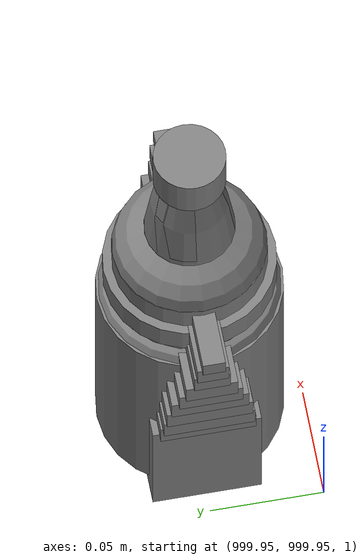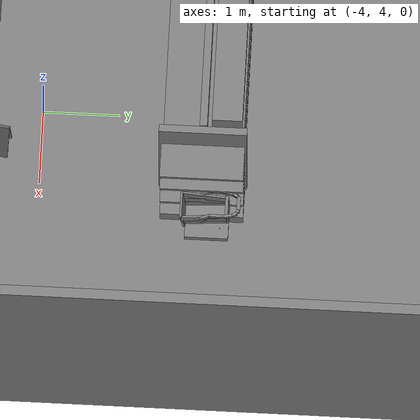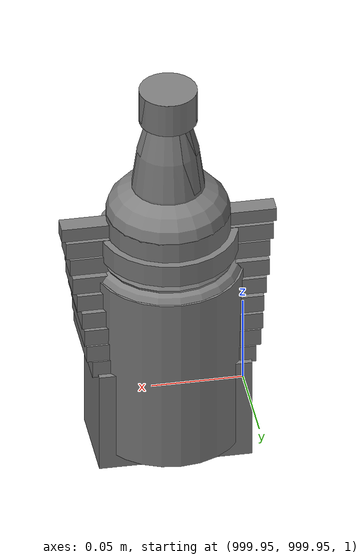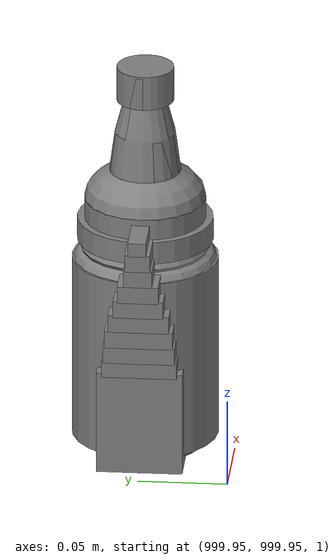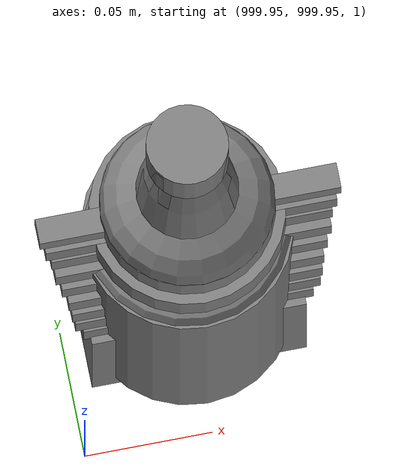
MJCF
<mujoco>
    <option gravity="0.000000000 0.000000000 -9.810000420" timestep="0.0166666" integrator="implicitfast" density="1.225" viscosity="1.8000001e-05" noslip_iterations="10" iterations="100" sdf_iterations="50">
        <flag multiccd="disable"/>
    </option>
    <size memory="1000M"/>
    <compiler coordinate="local"/>
    <worldbody>
        <light cutoff="30" pos="0 1 1" dir="0 -1 -2"/>
        <light cutoff="30" pos="0 -1 1" dir="0 1 -2"/>
        <body pos="-2.436573029 6.404376507 0.137849092" euler="0.000000000 0.000000000 0.000000000" name="openloong_gripper_2f85_fix_base_usda_shoppingtrolley_01">
            <geom contype="1" conaffinity="1" density="1000" type="box" material="" rgba="0.500000000 0.500000000 0.500000000 1.000000000" solimp="0.899999976 0.949999988 0.001000000" friction="1.000000000 0.005000000 0.000100000" solref="0.020000000 1.000000000" margin="0" condim="3" group="0" pos="-0.169898406 -0.178061336 0.864131629" quat="0.916343808 -0.400392294 -0.000000045 0.000000030" size="0.017999999 0.022499999 0.089999996" name="openloong_gripper_2f85_fix_base_usda_geom_87E7D483_E2E3_4271_98AC_39CAB8D732BA"/>
            <geom contype="1" conaffinity="1" density="1000" type="box" material="" rgba="0.500000000 0.500000000 0.500000000 1.000000000" solimp="0.899999976 0.949999988 0.001000000" friction="1.000000000 0.005000000 0.000100000" solref="0.020000000 1.000000000" margin="0" condim="3" group="0" pos="-0.107458733 0.238907143 0.911498845" quat="0.634576976 0.622505128 -0.330067992 -0.317575932" size="0.017999999 0.022499999 0.035999998" name="openloong_gripper_2f85_fix_base_usda_geom_10E7D3D1_0FBC_469A_B853_FB1DF00EC8C6"/>
            <geom contype="1" conaffinity="1" density="1000" type="box" material="" rgba="0.500000000 0.500000000 0.500000000 1.000000000" solimp="0.899999976 0.949999988 0.001000000" friction="1.000000000 0.005000000 0.000100000" solref="0.020000000 1.000000000" margin="0" condim="3" group="0" pos="-0.005004787 0.248085022 0.912686050" quat="1.000000000 0.000000000 0.000000000 0.000000000" size="0.107999995 0.022499999 0.022499999" name="openloong_gripper_2f85_fix_base_usda_geom_7E88D3B6_10A6_4C27_9436_0A3E097EB566"/>
            <geom contype="1" conaffinity="1" density="1000" type="box" material="" rgba="0.500000000 0.500000000 0.500000000 1.000000000" solimp="0.899999976 0.949999988 0.001000000" friction="1.000000000 0.005000000 0.000100000" solref="0.020000000 1.000000000" margin="0" condim="3" group="0" pos="0.131482959 -0.182533979 0.598989725" quat="0.996607125 0.055331629 0.059003670 0.015205893" size="0.013499999 0.287999988 0.053999998" name="openloong_gripper_2f85_fix_base_usda_geom_9D07620E_462D_49C2_B0D6_A721A28D2A10"/>
            <geom contype="1" conaffinity="1" density="1000" type="box" material="" rgba="0.500000000 0.500000000 0.500000000 1.000000000" solimp="0.899999976 0.949999988 0.001000000" friction="1.000000000 0.005000000 0.000100000" solref="0.020000000 1.000000000" margin="0" condim="3" group="0" pos="-0.000005364 0.100332208 0.734785020" quat="0.999668717 0.025737956 -0.000000010 0.000000000" size="0.135000005 0.019800000 0.152999997" name="openloong_gripper_2f85_fix_base_usda_geom_765AAAB8_1865_494E_86DA_70C9ECC65FBC"/>
            <geom contype="1" conaffinity="1" density="1000" type="box" material="" rgba="0.500000000 0.500000000 0.500000000 1.000000000" solimp="0.899999976 0.949999988 0.001000000" friction="1.000000000 0.005000000 0.000100000" solref="0.020000000 1.000000000" margin="0" condim="3" group="0" pos="-0.126757339 -0.182533979 0.598989725" quat="0.996607184 0.055331606 -0.059003651 -0.015205891" size="0.013499999 0.287999988 0.053999998" name="openloong_gripper_2f85_fix_base_usda_geom_39CBB369_4508_4465_93C8_A780667F04F7"/>
            <geom contype="1" conaffinity="1" density="1000" type="box" material="" rgba="0.500000000 0.500000000 0.500000000 1.000000000" solimp="0.899999976 0.949999988 0.001000000" friction="1.000000000 0.005000000 0.000100000" solref="0.020000000 1.000000000" margin="0" condim="3" group="0" pos="-0.134013891 0.200098798 0.912192523" quat="0.694057047 0.679413557 -0.172947660 -0.163618833" size="0.017999999 0.022499999 0.035999998" name="openloong_gripper_2f85_fix_base_usda_geom_5905F98F_E4DF_4558_81EF_248F48894E0A"/>
            <geom contype="1" conaffinity="1" density="1000" type="box" material="" rgba="0.500000000 0.500000000 0.500000000 1.000000000" solimp="0.899999976 0.949999988 0.001000000" friction="1.000000000 0.005000000 0.000100000" solref="0.020000000 1.000000000" margin="0" condim="3" group="0" pos="0.141839072 -0.191051379 0.702451229" quat="0.997147262 0.056065105 0.045779929 0.021407485" size="0.013499999 0.287999988 0.053999998" name="openloong_gripper_2f85_fix_base_usda_geom_FF0170D1_B7E6_41DF_A110_8F8D37BA03B5"/>
            <geom contype="1" conaffinity="1" density="1000" type="box" material="" rgba="0.500000000 0.500000000 0.500000000 1.000000000" solimp="0.899999976 0.949999988 0.001000000" friction="1.000000000 0.005000000 0.000100000" solref="0.020000000 1.000000000" margin="0" condim="3" group="0" pos="-0.135714188 -0.191051379 0.694841146" quat="0.997147322 0.056064609 -0.045779683 -0.021407485" size="0.013499999 0.287999988 0.053999998" name="openloong_gripper_2f85_fix_base_usda_geom_3900ED4A_13BE_443B_9002_77A55F036C04"/>
            <geom contype="1" conaffinity="1" density="1000" type="box" material="" rgba="0.500000000 0.500000000 0.500000000 1.000000000" solimp="0.899999976 0.949999988 0.001000000" friction="1.000000000 0.005000000 0.000100000" solref="0.020000000 1.000000000" margin="0" condim="3" group="0" pos="-0.000004721 -0.174527690 0.560063601" quat="0.996704638 0.081116498 -0.000000004 0.000000000" size="0.126000002 0.287999988 0.009000000" name="openloong_gripper_2f85_fix_base_usda_geom_342C7DF4_3C71_4492_BFF2_34AEEE20327B"/>
            <geom contype="1" conaffinity="1" density="1000" type="box" material="" rgba="0.500000000 0.500000000 0.500000000 1.000000000" solimp="0.899999976 0.949999988 0.001000000" friction="1.000000000 0.005000000 0.000100000" solref="0.020000000 1.000000000" margin="0" condim="3" group="0" pos="0.134013891 0.200098798 0.912192523" quat="0.692574680 -0.680924535 -0.166899428 0.169783980" size="0.017999999 0.022499999 0.035999998" name="openloong_gripper_2f85_fix_base_usda_geom_5CE2BE4A_4B9B_4BE7_892D_85E174608D3F"/>
            <geom contype="1" conaffinity="1" density="1000" type="box" material="" rgba="0.500000000 0.500000000 0.500000000 1.000000000" solimp="0.899999976 0.949999988 0.001000000" friction="1.000000000 0.005000000 0.000100000" solref="0.020000000 1.000000000" margin="0" condim="3" group="0" pos="-0.012634277 -0.174527690 -0.088243507" quat="1.000000000 0.000000000 -0.000000004 0.000000000" size="0.135000005 0.287999988 0.044999998" name="openloong_gripper_2f85_fix_base_usda_geom_13886C02_EA5D_415A_90E7_82EE5C56D755"/>
            <geom contype="1" conaffinity="1" density="1000" type="box" material="" rgba="0.500000000 0.500000000 0.500000000 1.000000000" solimp="0.899999976 0.949999988 0.001000000" friction="1.000000000 0.005000000 0.000100000" solref="0.020000000 1.000000000" margin="0" condim="3" group="0" pos="-0.142927840 -0.199506134 0.784674108" quat="0.998421252 0.016904408 -0.027109101 -0.046199299" size="0.013499999 0.305999994 0.063000001" name="openloong_gripper_2f85_fix_base_usda_geom_72E7C536_FFEC_4ED9_B5CC_33C470A199B2"/>
            <geom contype="1" conaffinity="1" density="1000" type="box" material="" rgba="0.500000000 0.500000000 0.500000000 1.000000000" solimp="0.899999976 0.949999988 0.001000000" friction="1.000000000 0.005000000 0.000100000" solref="0.020000000 1.000000000" margin="0" condim="3" group="0" pos="-0.169898406 -0.043119621 0.915120542" quat="0.687021017 0.726584017 -0.005590606 -0.006832919" size="0.017999999 0.022499999 0.089999996" name="openloong_gripper_2f85_fix_base_usda_geom_34F7D9A2_2EED_41CE_8152_AC3FA53FD315"/>
            <geom contype="1" conaffinity="1" density="1000" type="box" material="" rgba="0.500000000 0.500000000 0.500000000 1.000000000" solimp="0.899999976 0.949999988 0.001000000" friction="1.000000000 0.005000000 0.000100000" solref="0.020000000 1.000000000" margin="0" condim="3" group="0" pos="-0.000006008 -0.484932661 0.670727849" quat="0.997585475 0.069449045 -0.000000004 -0.000000089" size="0.179999992 0.013499999 0.170999989" name="openloong_gripper_2f85_fix_base_usda_geom_C9E0EC74_B316_43A7_BC83_BAEEA3B5D946"/>
            <geom contype="1" conaffinity="1" density="1000" type="box" material="" rgba="0.500000000 0.500000000 0.500000000 1.000000000" solimp="0.899999976 0.949999988 0.001000000" friction="1.000000000 0.005000000 0.000100000" solref="0.020000000 1.000000000" margin="0" condim="3" group="0" pos="0.160832971 0.103427693 0.910528183" quat="0.711112797 -0.700149298 -0.042821646 0.047705106" size="0.017999999 0.022499999 0.071999997" name="openloong_gripper_2f85_fix_base_usda_geom_6BAC5BC9_5278_4EBE_AD5C_63AFB887F349"/>
            <geom contype="1" conaffinity="1" density="1000" type="box" material="" rgba="0.500000000 0.500000000 0.500000000 1.000000000" solimp="0.899999976 0.949999988 0.001000000" friction="1.000000000 0.005000000 0.000100000" solref="0.020000000 1.000000000" margin="0" condim="3" group="0" pos="-0.160832763 0.103427693 0.910528183" quat="0.711469591 0.699786782 -0.048386075 -0.042050660" size="0.017999999 0.022499999 0.071999997" name="openloong_gripper_2f85_fix_base_usda_geom_4C4A6579_FB23_4D50_B200_07359E7E4566"/>
            <geom contype="1" conaffinity="1" density="1000" type="box" material="" rgba="0.500000000 0.500000000 0.500000000 1.000000000" solimp="0.899999976 0.949999988 0.001000000" friction="1.000000000 0.005000000 0.000100000" solref="0.020000000 1.000000000" margin="0" condim="3" group="0" pos="0.169898629 -0.178061336 0.864131629" quat="0.916343808 -0.400392294 -0.000000045 0.000000030" size="0.017999999 0.022499999 0.089999996" name="openloong_gripper_2f85_fix_base_usda_geom_B6C3F8B5_CA70_4FAF_A5C9_C671995FBF5F"/>
            <geom contype="1" conaffinity="1" density="1000" type="box" material="" rgba="0.500000000 0.500000000 0.500000000 1.000000000" solimp="0.899999976 0.949999988 0.001000000" friction="1.000000000 0.005000000 0.000100000" solref="0.020000000 1.000000000" margin="0" condim="3" group="0" pos="0.103667587 0.233050480 0.912927270" quat="0.634205043 -0.622199059 -0.324503720 0.324576139" size="0.017999999 0.022499999 0.035999998" name="openloong_gripper_2f85_fix_base_usda_geom_7010345F_4C50_424E_B288_F221CF145D47"/>
            <geom contype="1" conaffinity="1" density="1000" type="box" material="" rgba="0.500000000 0.500000000 0.500000000 1.000000000" solimp="0.899999976 0.949999988 0.001000000" friction="1.000000000 0.005000000 0.000100000" solref="0.020000000 1.000000000" margin="0" condim="3" group="0" pos="0.169898629 -0.043119621 0.915120542" quat="0.687029123 -0.726576388 -0.006509603 0.005963952" size="0.017999999 0.022499999 0.089999996" name="openloong_gripper_2f85_fix_base_usda_geom_C3AE13A6_52F7_4B79_978B_2BE0AF6508F5"/>
            <geom contype="1" conaffinity="1" density="1000" type="box" material="" rgba="0.500000000 0.500000000 0.500000000 1.000000000" solimp="0.899999976 0.949999988 0.001000000" friction="1.000000000 0.005000000 0.000100000" solref="0.020000000 1.000000000" margin="0" condim="3" group="0" pos="0.148195267 -0.199506566 0.782808602" quat="0.998808920 0.017156634 0.026950166 0.036880098" size="0.013499999 0.305999994 0.063000001" name="openloong_gripper_2f85_fix_base_usda_geom_AF139801_776F_44D7_B3D3_DF3015FDDEC7"/>
            <freejoint name="openloong_gripper_2f85_fix_base_usda_shoppingtrolley_01_joint"/>
            <site size="0.005000000 0.005000000 0.005000000" rgba="0.500000000 0.500000000 0.500000000 1.000000000" pos="0.000000000 0.000000000 0.000000000" quat="1.000000000 0.000000000 0.000000000 0.000000000" group="0" type="sphere" name="openloong_gripper_2f85_fix_base_usda_shoppingtrolley_01"/>
        </body>
        <body pos="-1.817611694 6.055809975 1.662208200" euler="26.980550766 33.402832031 125.338775635" mocap="true" name="spotlight5_SpotLight"/>
        <body pos="1000.000000000 1000.000000000 1.000000000" euler="0.000000000 0.000000000 0.000000000" name="openloong_gripper_2f85_fix_base_usda_can">
            <geom contype="1" conaffinity="1" density="1000" type="cylinder" material="" rgba="0.500000000 0.500000000 0.500000000 1.000000000" solimp="0.899999976 0.949999988 0.001000000" friction="1.000000000 0.005000000 0.000100000" solref="0.020000000 1.000000000" margin="0" condim="3" group="0" pos="0.000000000 0.000000000 0.079676986" quat="1.000000000 0.000000000 0.000000000 0.000000000" size="0.034000002 0.071999997 1.000000000" name="openloong_gripper_2f85_fix_base_usda_geom_F1AB2C80_180F_4E2A_A52B_B61D1EAA6D52"/>
            <geom contype="1" conaffinity="1" density="1000" type="ellipsoid" material="" rgba="0.500000000 0.500000000 0.500000000 1.000000000" solimp="0.899999976 0.949999988 0.001000000" friction="1.000000000 0.005000000 0.000100000" solref="0.020000000 1.000000000" margin="0" condim="3" group="0" pos="0.000000000 0.000000000 0.151854277" quat="1.000000000 0.000000000 0.000000000 0.000000000" size="0.034000002 0.034000002 0.020000000" name="openloong_gripper_2f85_fix_base_usda_geom_2F80F6C5_7799_4FFA_B249_43FFE9D53428"/>
            <geom contype="1" conaffinity="1" density="1000" type="box" material="" rgba="0.500000000 0.500000000 0.500000000 1.000000000" solimp="0.899999976 0.949999988 0.001000000" friction="1.000000000 0.005000000 0.000100000" solref="0.020000000 1.000000000" margin="0" condim="3" group="0" pos="0.000000000 0.000000000 0.004777670" quat="1.000000000 0.000000000 0.000000000 0.000000000" size="0.020000000 0.020000000 0.005000000" name="openloong_gripper_2f85_fix_base_usda_geom_2446683A_2615_4606_AD79_20CF2B0080F5"/>
            <freejoint name="openloong_gripper_2f85_fix_base_usda_can_joint"/>
            <site size="0.005000000 0.005000000 0.005000000" rgba="0.500000000 0.500000000 0.500000000 1.000000000" pos="0.000000000 0.000000000 0.000000000" quat="1.000000000 0.000000000 0.000000000 0.000000000" group="0" type="sphere" name="openloong_gripper_2f85_fix_base_usda_cansite"/>
        </body>
        <body pos="-2.210954666 6.191067219 1.731548429" euler="72.748191833 53.212291718 -163.124176025" mocap="true" name="spotlight2_SpotLight"/>
        <body pos="1000.000000000 1000.000000000 1.000000000" euler="0.000000000 0.000000000 0.000000000" name="openloong_gripper_2f85_fix_base_usda_salt">
            <geom contype="1" conaffinity="1" density="1000" type="box" material="" rgba="0.500000000 0.500000000 0.500000000 1.000000000" solimp="0.899999976 0.949999988 0.001000000" friction="1.000000000 0.005000000 0.000100000" solref="0.020000000 1.000000000" margin="0" condim="3" group="0" pos="0.000305176 0.000000000 0.084862232" quat="1.000000000 0.000000000 0.000000000 0.000000000" size="0.048999999 0.018999999 0.005000000" name="openloong_gripper_2f85_fix_base_usda_geom_BC907878_24DF_499B_8AD2_CE79E13F23C6"/>
            <geom contype="1" conaffinity="1" density="1000" type="box" material="" rgba="0.500000000 0.500000000 0.500000000 1.000000000" solimp="0.899999976 0.949999988 0.001000000" friction="1.000000000 0.005000000 0.000100000" solref="0.020000000 1.000000000" margin="0" condim="3" group="0" pos="0.000305176 0.000000000 0.104564309" quat="1.000000000 0.000000000 0.000000000 0.000000000" size="0.052000001 0.014000000 0.005000000" name="openloong_gripper_2f85_fix_base_usda_geom_D838CCDC_1680_4AAB_9834_E29B7999E603"/>
            <geom contype="1" conaffinity="1" density="1000" type="box" material="" rgba="0.500000000 0.500000000 0.500000000 1.000000000" solimp="0.899999976 0.949999988 0.001000000" friction="1.000000000 0.005000000 0.000100000" solref="0.020000000 1.000000000" margin="0" condim="3" group="0" pos="0.000305176 0.000000000 0.114487171" quat="1.000000000 0.000000000 0.000000000 0.000000000" size="0.054000001 0.011500000 0.005000000" name="openloong_gripper_2f85_fix_base_usda_geom_59F43005_CCF9_49F1_9F31_56F3EE8E986E"/>
            <geom contype="1" conaffinity="1" density="1000" type="box" material="" rgba="0.500000000 0.500000000 0.500000000 1.000000000" solimp="0.899999976 0.949999988 0.001000000" friction="1.000000000 0.005000000 0.000100000" solref="0.020000000 1.000000000" margin="0" condim="3" group="0" pos="0.000305176 0.000000000 0.075103164" quat="1.000000000 0.000000000 0.000000000 0.000000000" size="0.048000000 0.020000000 0.005000000" name="openloong_gripper_2f85_fix_base_usda_geom_D7B3DB01_1225_4501_9508_D0B56AFAE62B"/>
            <geom contype="1" conaffinity="1" density="1000" type="box" material="" rgba="0.500000000 0.500000000 0.500000000 1.000000000" solimp="0.899999976 0.949999988 0.001000000" friction="1.000000000 0.005000000 0.000100000" solref="0.020000000 1.000000000" margin="0" condim="3" group="0" pos="0.000305176 0.000000000 0.134892464" quat="1.000000000 0.000000000 0.000000000 0.000000000" size="0.057000000 0.007000000 0.005000000" name="openloong_gripper_2f85_fix_base_usda_geom_483E8D46_838D_492A_A342_2952B6DD1F5A"/>
            <geom contype="1" conaffinity="1" density="1000" type="box" material="" rgba="0.500000000 0.500000000 0.500000000 1.000000000" solimp="0.899999976 0.949999988 0.001000000" friction="1.000000000 0.005000000 0.000100000" solref="0.020000000 1.000000000" margin="0" condim="3" group="0" pos="0.000305176 0.000000000 0.094920278" quat="1.000000000 0.000000000 0.000000000 0.000000000" size="0.050000001 0.017000001 0.005000000" name="openloong_gripper_2f85_fix_base_usda_geom_7AC85E5C_D817_4EB3_BC1D_6D3B326640B6"/>
            <geom contype="1" conaffinity="1" density="1000" type="box" material="" rgba="0.500000000 0.500000000 0.500000000 1.000000000" solimp="0.899999976 0.949999988 0.001000000" friction="1.000000000 0.005000000 0.000100000" solref="0.020000000 1.000000000" margin="0" condim="3" group="0" pos="0.000305176 0.000000000 0.065204859" quat="1.000000000 0.000000000 0.000000000 0.000000000" size="0.045000002 0.021000000 0.005000000" name="openloong_gripper_2f85_fix_base_usda_geom_64C76B5C_A695_4A22_B51F_406C5F97456F"/>
            <geom contype="1" conaffinity="1" density="1000" type="box" material="" rgba="0.500000000 0.500000000 0.500000000 1.000000000" solimp="0.899999976 0.949999988 0.001000000" friction="1.000000000 0.005000000 0.000100000" solref="0.020000000 1.000000000" margin="0" condim="3" group="0" pos="0.000305176 0.000000000 0.144135714" quat="1.000000000 0.000000000 0.000000000 0.000000000" size="0.059000000 0.005000000 0.004000000" name="openloong_gripper_2f85_fix_base_usda_geom_21001834_0ABC_42B9_878C_932B6A030AC8"/>
            <geom contype="1" conaffinity="1" density="1000" type="box" material="" rgba="0.500000000 0.500000000 0.500000000 1.000000000" solimp="0.899999976 0.949999988 0.001000000" friction="1.000000000 0.005000000 0.000100000" solref="0.020000000 1.000000000" margin="0" condim="3" group="0" pos="0.000000000 0.000000000 0.031593561" quat="1.000000000 0.000000000 0.000000000 0.000000000" size="0.041999999 0.024000000 0.029999999" name="openloong_gripper_2f85_fix_base_usda_geom_A10C4E7B_A7AC_4CF7_A69B_B9573DA13D2A"/>
            <geom contype="1" conaffinity="1" density="1000" type="box" material="" rgba="0.500000000 0.500000000 0.500000000 1.000000000" solimp="0.899999976 0.949999988 0.001000000" friction="1.000000000 0.005000000 0.000100000" solref="0.020000000 1.000000000" margin="0" condim="3" group="0" pos="0.000305176 0.000000000 0.124608755" quat="1.000000000 0.000000000 0.000000000 0.000000000" size="0.055000000 0.008000000 0.005000000" name="openloong_gripper_2f85_fix_base_usda_geom_771AC97F_03F4_446B_9409_81A39D52CC01"/>
            <freejoint name="openloong_gripper_2f85_fix_base_usda_salt_joint"/>
            <site size="0.005000000 0.005000000 0.005000000" rgba="0.500000000 0.500000000 0.500000000 1.000000000" pos="0.000000000 0.000000000 0.000000000" quat="1.000000000 0.000000000 0.000000000 0.000000000" group="0" type="sphere" name="openloong_gripper_2f85_fix_base_usda_saltsite"/>
        </body>
        <body pos="1000.000000000 1000.000000000 1.000000000" euler="0.000000000 0.000000000 0.000000000" name="openloong_gripper_2f85_fix_base_usda_bottle_red">
            <geom contype="1" conaffinity="1" density="1000" type="ellipsoid" material="" rgba="0.500000000 0.500000000 0.500000000 1.000000000" solimp="0.899999976 0.949999988 0.001000000" friction="1.000000000 0.005000000 0.000100000" solref="0.020000000 1.000000000" margin="0" condim="3" group="0" pos="0.000000000 0.000000000 0.144284487" quat="1.000000000 0.000000000 0.000000000 0.000000000" size="0.021000000 0.021000000 0.079999998" name="openloong_gripper_2f85_fix_base_usda_geom_6A860FB7_D056_479C_8D21_D926CBD01B11"/>
            <geom contype="1" conaffinity="1" density="1000" type="cylinder" material="" rgba="0.500000000 0.500000000 0.500000000 1.000000000" solimp="0.899999976 0.949999988 0.001000000" friction="1.000000000 0.005000000 0.000100000" solref="0.020000000 1.000000000" margin="0" condim="3" group="0" pos="0.000000000 0.000000000 0.220618963" quat="1.000000000 0.000000000 0.000000000 0.000000000" size="0.016000001 0.010000000 1.000000000" name="openloong_gripper_2f85_fix_base_usda_geom_7C52BE3C_E445_4A7B_AC7A_3B0F6B59F71B"/>
            <geom contype="1" conaffinity="1" density="1000" type="ellipsoid" material="" rgba="0.500000000 0.500000000 0.500000000 1.000000000" solimp="0.899999976 0.949999988 0.001000000" friction="1.000000000 0.005000000 0.000100000" solref="0.020000000 1.000000000" margin="0" condim="3" group="0" pos="0.000000000 0.000000000 0.118945479" quat="1.000000000 0.000000000 0.000000000 0.000000000" size="0.030999999 0.030999999 0.029999999" name="openloong_gripper_2f85_fix_base_usda_geom_A109939D_DFB4_4B20_A13C_8B7CECF01E8E"/>
            <geom contype="1" conaffinity="1" density="1000" type="box" material="" rgba="0.500000000 0.500000000 0.500000000 1.000000000" solimp="0.899999976 0.949999988 0.001000000" friction="1.000000000 0.005000000 0.000100000" solref="0.020000000 1.000000000" margin="0" condim="3" group="0" pos="0.000000000 0.000000000 0.002189159" quat="1.000000000 0.000000000 0.000000000 0.000000000" size="0.020000000 0.020000000 0.003000000" name="openloong_gripper_2f85_fix_base_usda_geom_BF2489D4_C650_4E02_8D51_762F977CF497"/>
            <geom contype="1" conaffinity="1" density="1000" type="cylinder" material="" rgba="0.500000000 0.500000000 0.500000000 1.000000000" solimp="0.899999976 0.949999988 0.001000000" friction="1.000000000 0.005000000 0.000100000" solref="0.020000000 1.000000000" margin="0" condim="3" group="0" pos="0.000000000 -0.000366211 0.060884237" quat="1.000000000 0.000000000 0.000000000 0.000000000" size="0.030999999 0.057999998 1.000000000" name="openloong_gripper_2f85_fix_base_usda_geom_CA4CB52A_61B8_436E_98CF_0FC2188CA3A7"/>
            <freejoint name="openloong_gripper_2f85_fix_base_usda_bottle_red_joint"/>
            <site size="0.005000000 0.005000000 0.005000000" rgba="0.500000000 0.500000000 0.500000000 1.000000000" pos="0.000000000 0.000000000 0.000000000" quat="0.999961913 0.008726535 0.000000000 0.000000000" group="0" type="sphere" name="openloong_gripper_2f85_fix_base_usda_bottle_redsite"/>
        </body>
        <body pos="1000.000000000 1000.000000000 1.000000000" euler="0.000000000 0.000000000 0.000000000" name="openloong_gripper_2f85_fix_base_usda_jar_01">
            <geom contype="1" conaffinity="1" density="1000" type="box" material="" rgba="0.500000000 0.500000000 0.500000000 1.000000000" solimp="0.899999976 0.949999988 0.001000000" friction="1.000000000 0.005000000 0.000100000" solref="0.020000000 1.000000000" margin="0" condim="3" group="0" pos="0.000000000 0.000000000 0.006158113" quat="1.000000000 0.000000000 0.000000000 0.000000000" size="0.020000000 0.020000000 0.005000000" name="openloong_gripper_2f85_fix_base_usda_geom_9469095D_D88F_499C_AC64_B3FF90DA7097"/>
            <geom contype="1" conaffinity="1" density="1000" type="cylinder" material="" rgba="0.500000000 0.500000000 0.500000000 1.000000000" solimp="0.899999976 0.949999988 0.001000000" friction="1.000000000 0.005000000 0.000100000" solref="0.020000000 1.000000000" margin="0" condim="3" group="0" pos="0.000000000 0.000000000 0.062744498" quat="1.000000000 0.000000000 0.000000000 0.000000000" size="0.041000001 0.052999999 1.000000000" name="openloong_gripper_2f85_fix_base_usda_geom_460E73AE_DBAD_4C2C_ADDA_31A197B3748F"/>
            <geom contype="1" conaffinity="1" density="1000" type="ellipsoid" material="" rgba="0.500000000 0.500000000 0.500000000 1.000000000" solimp="0.899999976 0.949999988 0.001000000" friction="1.000000000 0.005000000 0.000100000" solref="0.020000000 1.000000000" margin="0" condim="3" group="0" pos="0.000000000 0.000000000 0.122252703" quat="1.000000000 0.000000000 0.000000000 0.000000000" size="0.035999998 0.035999998 0.010000000" name="openloong_gripper_2f85_fix_base_usda_geom_DDE0F1D2_C47A_44DB_9A3C_83A48D1A0A4B"/>
            <geom contype="1" conaffinity="1" density="1000" type="cylinder" material="" rgba="0.500000000 0.500000000 0.500000000 1.000000000" solimp="0.899999976 0.949999988 0.001000000" friction="1.000000000 0.005000000 0.000100000" solref="0.020000000 1.000000000" margin="0" condim="3" group="0" pos="0.000000000 0.000000000 0.015747190" quat="1.000000000 0.000000000 0.000000000 0.000000000" size="0.035000000 0.010000000 1.000000000" name="openloong_gripper_2f85_fix_base_usda_geom_C7F24A2D_6255_490C_AA87_3CF15A6F8B4A"/>
            <geom contype="1" conaffinity="1" density="1000" type="ellipsoid" material="" rgba="0.500000000 0.500000000 0.500000000 1.000000000" solimp="0.899999976 0.949999988 0.001000000" friction="1.000000000 0.005000000 0.000100000" solref="0.020000000 1.000000000" margin="0" condim="3" group="0" pos="0.000000000 0.000000000 0.115815401" quat="1.000000000 0.000000000 0.000000000 0.000000000" size="0.039999999 0.039999999 0.010000000" name="openloong_gripper_2f85_fix_base_usda_geom_73468C85_7174_4A8C_892A_0FDB4FFB697D"/>
            <geom contype="1" conaffinity="1" density="1000" type="cylinder" material="" rgba="0.500000000 0.500000000 0.500000000 1.000000000" solimp="0.899999976 0.949999988 0.001000000" friction="1.000000000 0.005000000 0.000100000" solref="0.020000000 1.000000000" margin="0" condim="3" group="0" pos="0.000000000 0.000000000 0.133183479" quat="1.000000000 0.000000000 0.000000000 0.000000000" size="0.037999999 0.006500000 1.000000000" name="openloong_gripper_2f85_fix_base_usda_geom_7E49545A_3BD8_4AE7_B8D1_F10BC65826FC"/>
            <freejoint name="openloong_gripper_2f85_fix_base_usda_jar_01_joint"/>
            <site size="0.005000000 0.005000000 0.005000000" rgba="0.500000000 0.500000000 0.500000000 1.000000000" pos="0.000000000 0.000000000 0.000000000" quat="1.000000000 0.000000000 0.000000000 0.000000000" group="0" type="sphere" name="openloong_gripper_2f85_fix_base_usda_jar_01site"/>
        </body>
        <body pos="1000.000000000 1000.000000000 1.000000000" euler="0.000000000 0.000000000 0.000000000" name="openloong_gripper_2f85_fix_base_usda_bottle_blue">
            <geom contype="1" conaffinity="1" density="1000" type="ellipsoid" material="" rgba="0.500000000 0.500000000 0.500000000 1.000000000" solimp="0.899999976 0.949999988 0.001000000" friction="1.000000000 0.005000000 0.000100000" solref="0.020000000 1.000000000" margin="0" condim="3" group="0" pos="0.000000000 0.000000000 0.118920922" quat="1.000000000 0.000000000 0.000000000 0.000000000" size="0.030999999 0.030999999 0.029999999" name="openloong_gripper_2f85_fix_base_usda_geom_30C92ACF_13AF_434F_9D1A_8FBE6DF42122"/>
            <geom contype="1" conaffinity="1" density="1000" type="box" material="" rgba="0.500000000 0.500000000 0.500000000 1.000000000" solimp="0.899999976 0.949999988 0.001000000" friction="1.000000000 0.005000000 0.000100000" solref="0.020000000 1.000000000" margin="0" condim="3" group="0" pos="0.000000000 0.000000000 0.002164602" quat="1.000000000 0.000000000 0.000000000 0.000000000" size="0.020000000 0.020000000 0.003000000" name="openloong_gripper_2f85_fix_base_usda_geom_D921B39D_C12A_44E6_B71E_02479F9361D5"/>
            <geom contype="1" conaffinity="1" density="1000" type="cylinder" material="" rgba="0.500000000 0.500000000 0.500000000 1.000000000" solimp="0.899999976 0.949999988 0.001000000" friction="1.000000000 0.005000000 0.000100000" solref="0.020000000 1.000000000" margin="0" condim="3" group="0" pos="0.000000000 -0.000366211 0.060859680" quat="1.000000000 0.000000000 0.000000000 0.000000000" size="0.030999999 0.057999998 1.000000000" name="openloong_gripper_2f85_fix_base_usda_geom_88397B6A_3072_4BB3_8A26_7DF0311F0DCA"/>
            <geom contype="1" conaffinity="1" density="1000" type="cylinder" material="" rgba="0.500000000 0.500000000 0.500000000 1.000000000" solimp="0.899999976 0.949999988 0.001000000" friction="1.000000000 0.005000000 0.000100000" solref="0.020000000 1.000000000" margin="0" condim="3" group="0" pos="0.000000000 0.000000000 0.220594406" quat="1.000000000 0.000000000 0.000000000 0.000000000" size="0.016000001 0.010000000 1.000000000" name="openloong_gripper_2f85_fix_base_usda_geom_151A2B89_64D0_43D7_A6F6_D8ADC9655119"/>
            <geom contype="1" conaffinity="1" density="1000" type="ellipsoid" material="" rgba="0.500000000 0.500000000 0.500000000 1.000000000" solimp="0.899999976 0.949999988 0.001000000" friction="1.000000000 0.005000000 0.000100000" solref="0.020000000 1.000000000" margin="0" condim="3" group="0" pos="0.000000000 0.000000000 0.144259930" quat="1.000000000 0.000000000 0.000000000 0.000000000" size="0.021000000 0.021000000 0.079999998" name="openloong_gripper_2f85_fix_base_usda_geom_E8B8F656_3A1F_442C_9910_42F564A83F29"/>
            <freejoint name="openloong_gripper_2f85_fix_base_usda_bottle_blue_joint"/>
            <site size="0.005000000 0.005000000 0.005000000" rgba="0.500000000 0.500000000 0.500000000 1.000000000" pos="0.000000000 0.000000000 0.000000000" quat="0.999961913 0.008726535 0.000000000 0.000000000" group="0" type="sphere" name="openloong_gripper_2f85_fix_base_usda_bottle_bluesite"/>
        </body>
        <body pos="-1.847580433 5.929386139 1.691771507" euler="21.922765732 26.136022568 38.308544159" mocap="true" name="spotlight4_SpotLight"/>
        <body pos="0.000000000 0.000000000 0.000000000" euler="0.000000000 0.000000000 0.000000000" name=" Static Objects_ Static Objects">
            <geom contype="1" conaffinity="1" density="1000" type="box" material="" rgba="0.500000000 0.500000000 0.500000000 1.000000000" solimp="0.899999976 0.949999988 0.001000000" friction="1.000000000 0.005000000 0.000100000" solref="0.020000000 1.000000000" margin="0" condim="3" group="0" pos="-3.101639986 6.150595188 1.018643856" quat="1.000000000 0.000000000 0.000000000 0.000000000" size="0.050000001 0.579999983 1.019999981" name=" Static Objects_geom_F37143E7_8094_49D2_A890_6F220E1577F8"/>
            <geom contype="1" conaffinity="1" density="1000" type="box" material="" rgba="0.500000000 0.500000000 0.500000000 1.000000000" solimp="0.899999976 0.949999988 0.001000000" friction="1.000000000 0.005000000 0.000100000" solref="0.020000000 1.000000000" margin="0" condim="3" group="0" pos="-2.825197220 6.153595448 1.115278244" quat="0.707107067 0.000000000 0.000000000 0.707106471" size="0.550000012 0.239999995 0.025000000" name=" Static Objects_geom_9B4CF04C_E3A0_4D9F_994C_4AAFD77E2C63"/>
            <geom contype="1" conaffinity="1" density="1000" type="box" material="" rgba="0.500000000 0.500000000 0.500000000 1.000000000" solimp="0.899999976 0.949999988 0.001000000" friction="1.000000000 0.005000000 0.000100000" solref="0.020000000 1.000000000" margin="0" condim="3" group="0" pos="-2.825197220 6.153595448 0.097434282" quat="0.707107067 0.000000000 0.000000000 0.707106471" size="0.550000012 0.239999995 0.098999999" name=" Static Objects_geom_F744A36E_93BF_413E_A54C_A585375685B3"/>
            <geom contype="1" conaffinity="1" density="1000" type="box" material="" rgba="0.500000000 0.500000000 0.500000000 1.000000000" solimp="0.899999976 0.949999988 0.001000000" friction="1.000000000 0.005000000 0.000100000" solref="0.020000000 1.000000000" margin="0" condim="3" group="0" pos="-6.293097973 6.153595448 1.114443064" quat="0.707107067 0.000000000 0.000000000 0.707106471" size="0.529999971 3.134999990 0.025000000" name=" Static Objects_geom_9217724F_30DF_471D_9567_D45CA3F7AE5E"/>
            <geom contype="1" conaffinity="1" density="1000" type="box" material="" rgba="0.500000000 0.500000000 0.500000000 1.000000000" solimp="0.899999976 0.949999988 0.001000000" friction="1.000000000 0.005000000 0.000100000" solref="0.020000000 1.000000000" margin="0" condim="3" group="0" pos="-6.286010742 6.153595448 0.096129179" quat="0.707107067 0.000000000 0.000000000 0.707106471" size="0.529999971 3.134999990 0.098999999" name=" Static Objects_geom_A8A0693A_16C5_45EB_B478_AC2615E62658"/>
            <geom contype="1" conaffinity="1" density="1000" type="box" material="" rgba="0.500000000 0.500000000 0.500000000 1.000000000" solimp="0.899999976 0.949999988 0.001000000" friction="1.000000000 0.005000000 0.000100000" solref="0.020000000 1.000000000" margin="0" condim="3" group="0" pos="-2.825197220 6.153595448 1.563861728" quat="0.707107067 0.000000000 0.000000000 0.707106471" size="0.550000012 0.239999995 0.025000000" name=" Static Objects_geom_FB8727EC_96EE_436D_B89F_2A5C796527D7"/>
            <geom contype="1" conaffinity="1" density="1000" type="box" material="" rgba="0.500000000 0.500000000 0.500000000 1.000000000" solimp="0.899999976 0.949999988 0.001000000" friction="1.000000000 0.005000000 0.000100000" solref="0.020000000 1.000000000" margin="0" condim="3" group="0" pos="-6.311686516 6.153595448 1.018643856" quat="0.707107067 0.000000000 0.000000000 0.707106471" size="0.050000001 3.150000095 1.019999981" name=" Static Objects_geom_19CA6FC0_3D0F_40BB_98B1_618BED4ACB26"/>
            <geom contype="1" conaffinity="1" density="1000" type="box" material="" rgba="0.500000000 0.500000000 0.500000000 1.000000000" solimp="0.899999976 0.949999988 0.001000000" friction="1.000000000 0.005000000 0.000100000" solref="0.020000000 1.000000000" margin="0" condim="3" group="0" pos="-2.825197220 6.153595448 0.629031777" quat="0.707107067 0.000000000 0.000000000 0.707106471" size="0.550000012 0.239999995 0.025000000" name=" Static Objects_geom_EBBAB02C_404C_4E98_BB44_CED9C3486582"/>
            <geom contype="1" conaffinity="1" density="1000" type="box" material="" rgba="0.500000000 0.500000000 0.500000000 1.000000000" solimp="0.899999976 0.949999988 0.001000000" friction="1.000000000 0.005000000 0.000100000" solref="0.020000000 1.000000000" margin="0" condim="3" group="0" pos="-6.286010742 6.153595448 1.563861728" quat="0.707107067 0.000000000 0.000000000 0.707106471" size="0.529999971 3.134999990 0.025000000" name=" Static Objects_geom_0C6FFD5C_EE8B_4F80_BD2C_05911701860C"/>
            <geom contype="1" conaffinity="1" density="1000" type="box" material="" rgba="0.500000000 0.500000000 0.500000000 1.000000000" solimp="0.899999976 0.949999988 0.001000000" friction="1.000000000 0.005000000 0.000100000" solref="0.020000000 1.000000000" margin="0" condim="3" group="0" pos="-6.286010742 6.153595448 0.629031777" quat="0.707107067 0.000000000 0.000000000 0.707106471" size="0.529999971 3.134999990 0.025000000" name=" Static Objects_geom_FF209A48_56A3_4BCE_A24F_E9539405CFD5"/>
            <geom contype="1" conaffinity="1" density="1000" type="box" material="" rgba="0.500000000 0.500000000 0.500000000 1.000000000" solimp="0.899999976 0.949999988 0.001000000" friction="1.000000000 0.005000000 0.000100000" solref="0.020000000 1.000000000" margin="0" condim="3" group="0" pos="-7.719123363 2.867671013 1.173410416" quat="1.000000000 0.000000000 0.000000000 0.000000000" size="0.250000000 0.250000000 0.079999998" name=" Static Objects_geom_BC1E89AD_ACDD_473F_A786_8A65501260C5"/>
            <geom contype="1" conaffinity="1" density="1000" type="box" material="" rgba="0.500000000 0.500000000 0.500000000 1.000000000" solimp="0.899999976 0.949999988 0.001000000" friction="1.000000000 0.005000000 0.000100000" solref="0.020000000 1.000000000" margin="0" condim="3" group="0" pos="-7.408766270 3.088089943 1.776644945" quat="0.928051054 0.000000000 0.000000000 0.372453064" size="0.050000001 0.100000001 0.050000001" name=" Static Objects_geom_87479CA7_FA18_44F9_8D80_354748A50D38"/>
            <geom contype="1" conaffinity="1" density="1000" type="box" material="" rgba="0.500000000 0.500000000 0.500000000 1.000000000" solimp="0.899999976 0.949999988 0.001000000" friction="1.000000000 0.005000000 0.000100000" solref="0.020000000 1.000000000" margin="0" condim="3" group="0" pos="-7.719123363 2.958004713 1.530241251" quat="1.000000000 0.000000000 0.000000000 0.000000000" size="0.250000000 0.159999996 0.280000001" name=" Static Objects_geom_E2E764D7_9484_4A11_A1E1_30DC8E2D6EC8"/>
            <geom contype="1" conaffinity="1" density="1000" type="cylinder" material="" rgba="0.500000000 0.500000000 0.500000000 1.000000000" solimp="0.899999976 0.949999988 0.001000000" friction="1.000000000 0.005000000 0.000100000" solref="0.020000000 1.000000000" margin="0" condim="3" group="0" pos="-7.427312374 3.069516420 1.502544641" quat="0.928051054 0.000000000 0.000000000 0.372453064" size="0.015000000 0.230000004 0.100000001" name=" Static Objects_geom_850BCF51_CA7B_4809_83D5_9003A7503484"/>
            <geom contype="1" conaffinity="1" density="1000" type="box" material="" rgba="0.500000000 0.500000000 0.500000000 1.000000000" solimp="0.899999976 0.949999988 0.001000000" friction="1.000000000 0.005000000 0.000100000" solref="0.020000000 1.000000000" margin="0" condim="3" group="0" pos="-7.437745571 3.067511320 1.289965630" quat="1.000000000 0.000000000 0.000000000 0.000000000" size="0.029999999 0.020000000 0.020000000" name=" Static Objects_geom_703636BD_EB8B_46AF_A2FC_77BFC1F26F29"/>
            <geom contype="1" conaffinity="1" density="1000" type="box" material="" rgba="0.500000000 0.500000000 0.500000000 1.000000000" solimp="0.899999976 0.949999988 0.001000000" friction="1.000000000 0.005000000 0.000100000" solref="0.020000000 1.000000000" margin="0" condim="3" group="0" pos="-9.058088303 6.434794426 1.209077358" quat="1.000000000 0.000000000 0.000000000 0.000000000" size="0.250000000 0.100000001 0.070000000" name=" Static Objects_geom_A4FEB7F3_B73F_48E1_9DB6_566C0F39516E"/>
            <geom contype="1" conaffinity="1" density="1000" type="box" material="" rgba="0.500000000 0.500000000 0.500000000 1.000000000" solimp="0.899999976 0.949999988 0.001000000" friction="1.000000000 0.005000000 0.000100000" solref="0.020000000 1.000000000" margin="0" condim="3" group="0" pos="-7.886891365 6.459744930 0.352518857" quat="1.000000000 0.000000000 0.000000000 0.000000000" size="1.500000000 0.200000003 0.150000006" name=" Static Objects_geom_E4D627F0_0002_415D_BBF7_B0086A9B5552"/>
            <geom contype="1" conaffinity="1" density="1000" type="box" material="" rgba="0.500000000 0.500000000 0.500000000 1.000000000" solimp="0.899999976 0.949999988 0.001000000" friction="1.000000000 0.005000000 0.000100000" solref="0.020000000 1.000000000" margin="0" condim="3" group="0" pos="-9.237723351 6.464855671 1.209077358" quat="1.000000000 0.000000000 0.000000000 0.000000000" size="0.100000001 0.100000001 0.070000000" name=" Static Objects_geom_D488DA1A_EC27_429B_A8DE_E578F3DA15F7"/>
            <geom contype="1" conaffinity="1" density="1000" type="box" material="" rgba="0.500000000 0.500000000 0.500000000 1.000000000" solimp="0.899999976 0.949999988 0.001000000" friction="1.000000000 0.005000000 0.000100000" solref="0.020000000 1.000000000" margin="0" condim="3" group="0" pos="-6.924745083 6.362090111 1.214329123" quat="1.000000000 0.000000000 0.000000000 0.000000000" size="0.200000003 0.100000001 0.075000003" name=" Static Objects_geom_A5B553E4_CCD3_45FA_B9B3_BEAB291A639B"/>
            <geom contype="1" conaffinity="1" density="1000" type="box" material="" rgba="0.500000000 0.500000000 0.500000000 1.000000000" solimp="0.899999976 0.949999988 0.001000000" friction="1.000000000 0.005000000 0.000100000" solref="0.020000000 1.000000000" margin="0" condim="3" group="0" pos="-4.407354832 6.459744930 1.292199373" quat="1.000000000 0.000000000 0.000000000 0.000000000" size="1.240000010 0.200000003 0.150000006" name=" Static Objects_geom_D08A7203_129C_46D4_9D2A_D54057EA7B84"/>
            <geom contype="1" conaffinity="1" density="1000" type="box" material="" rgba="0.500000000 0.500000000 0.500000000 1.000000000" solimp="0.899999976 0.949999988 0.001000000" friction="1.000000000 0.005000000 0.000100000" solref="0.020000000 1.000000000" margin="0" condim="3" group="0" pos="-5.611940861 6.318420410 0.350975692" quat="1.000000000 0.000000000 0.000000000 0.000000000" size="0.699999988 0.100000001 0.150000006" name=" Static Objects_geom_599E747E_E0E5_4B0F_A924_87AAA5C5D6DE"/>
            <geom contype="1" conaffinity="1" density="1000" type="box" material="" rgba="0.500000000 0.500000000 0.500000000 1.000000000" solimp="0.899999976 0.949999988 0.001000000" friction="1.000000000 0.005000000 0.000100000" solref="0.020000000 1.000000000" margin="0" condim="3" group="0" pos="-6.300771236 6.459744930 1.744376063" quat="1.000000000 0.000000000 0.000000000 0.000000000" size="3.000000000 0.200000003 0.150000006" name=" Static Objects_geom_DA6DDC76_A9B9_41CA_8084_7B3A202B64DF"/>
            <geom contype="1" conaffinity="1" density="1000" type="box" material="" rgba="0.500000000 0.500000000 0.500000000 1.000000000" solimp="0.899999976 0.949999988 0.001000000" friction="1.000000000 0.005000000 0.000100000" solref="0.020000000 1.000000000" margin="0" condim="3" group="0" pos="-6.751636982 6.459744930 0.800981164" quat="1.000000000 0.000000000 0.000000000 0.000000000" size="2.200000048 0.200000003 0.150000006" name=" Static Objects_geom_4EF4160C_1019_4848_801B_08FD5661A681"/>
            <geom contype="1" conaffinity="1" density="1000" type="box" material="" rgba="0.500000000 0.500000000 0.500000000 1.000000000" solimp="0.899999976 0.949999988 0.001000000" friction="1.000000000 0.005000000 0.000100000" solref="0.020000000 1.000000000" margin="0" condim="3" group="0" pos="-8.844120979 6.464855671 1.209077358" quat="1.000000000 0.000000000 0.000000000 0.000000000" size="0.100000001 0.100000001 0.070000000" name=" Static Objects_geom_1EDE3379_5771_4A02_B0AC_619CB57AB347"/>
            <geom contype="1" conaffinity="1" density="1000" type="box" material="" rgba="0.500000000 0.500000000 0.500000000 1.000000000" solimp="0.899999976 0.949999988 0.001000000" friction="1.000000000 0.005000000 0.000100000" solref="0.020000000 1.000000000" margin="0" condim="3" group="0" pos="-6.098561764 6.327973843 1.292199373" quat="1.000000000 0.000000000 0.000000000 0.000000000" size="0.500000000 0.100000001 0.150000006" name=" Static Objects_geom_94BB6876_83A6_4C38_9BFC_38AB6724D082"/>
            <geom contype="1" conaffinity="1" density="1000" type="box" material="" rgba="0.500000000 0.500000000 0.500000000 1.000000000" solimp="0.899999976 0.949999988 0.001000000" friction="1.000000000 0.005000000 0.000100000" solref="0.020000000 1.000000000" margin="0" condim="3" group="0" pos="-6.824534416 6.447464466 1.212718010" quat="1.000000000 0.000000000 0.000000000 0.000000000" size="0.100000001 0.100000001 0.075000003" name=" Static Objects_geom_0B40BE49_1289_434C_BF1A_94C8B411E9C4"/>
            <geom contype="1" conaffinity="1" density="1000" type="box" material="" rgba="0.500000000 0.500000000 0.500000000 1.000000000" solimp="0.899999976 0.949999988 0.001000000" friction="1.000000000 0.005000000 0.000100000" solref="0.020000000 1.000000000" margin="0" condim="3" group="0" pos="-3.907610416 6.318625927 0.800981164" quat="1.000000000 0.000000000 0.000000000 0.000000000" size="0.500000000 0.100000001 0.150000006" name=" Static Objects_geom_F47C4298_CE6F_4EE4_A287_AA67E4966430"/>
            <geom contype="1" conaffinity="1" density="1000" type="box" material="" rgba="0.500000000 0.500000000 0.500000000 1.000000000" solimp="0.899999976 0.949999988 0.001000000" friction="1.000000000 0.005000000 0.000100000" solref="0.020000000 1.000000000" margin="0" condim="3" group="0" pos="-7.373087406 6.458900928 1.214329123" quat="1.000000000 0.000000000 0.000000000 0.000000000" size="0.250000000 0.200000003 0.075000003" name=" Static Objects_geom_A4D1A4F8_63D6_41B4_8221_FDA307BBF411"/>
            <geom contype="1" conaffinity="1" density="1000" type="box" material="" rgba="0.500000000 0.500000000 0.500000000 1.000000000" solimp="0.899999976 0.949999988 0.001000000" friction="1.000000000 0.005000000 0.000100000" solref="0.020000000 1.000000000" margin="0" condim="3" group="0" pos="-4.035642624 6.459744930 0.352518857" quat="1.000000000 0.000000000 0.000000000 0.000000000" size="0.800000012 0.200000003 0.150000006" name=" Static Objects_geom_03C5FFCD_D090_4BA5_B0BE_F183F937F3B5"/>
            <geom contype="1" conaffinity="1" density="1000" type="box" material="" rgba="0.500000000 0.500000000 0.500000000 1.000000000" solimp="0.899999976 0.949999988 0.001000000" friction="1.000000000 0.005000000 0.000100000" solref="0.020000000 1.000000000" margin="0" condim="3" group="0" pos="-6.460197449 2.937205315 0.548931718" quat="1.000000000 0.000000000 0.000000000 0.000000000" size="2.650000095 0.430000007 0.550000012" name=" Static Objects_geom_BDC8D831_A13E_4037_BECE_D3E7C32520BF"/>
            <geom contype="1" conaffinity="1" density="1000" type="box" material="" rgba="0.500000000 0.500000000 0.500000000 1.000000000" solimp="0.899999976 0.949999988 0.001000000" friction="1.000000000 0.005000000 0.000100000" solref="0.020000000 1.000000000" margin="0" condim="3" group="0" pos="-4.240264893 1.327049494 0.549888909" quat="1.000000000 0.000000000 0.000000000 0.000000000" size="0.430000007 1.200000048 0.550000012" name=" Static Objects_geom_03399DE3_4E1E_438A_B334_0C126945F5B9"/>
            <geom contype="1" conaffinity="1" density="1000" type="box" material="" rgba="0.500000000 0.500000000 0.500000000 1.000000000" solimp="0.899999976 0.949999988 0.001000000" friction="1.000000000 0.005000000 0.000100000" solref="0.020000000 1.000000000" margin="0" condim="3" group="0" pos="-8.830721855 2.096410990 0.549305558" quat="1.000000000 0.000000000 0.000000000 0.000000000" size="0.280000001 0.430000007 0.550000012" name=" Static Objects_geom_44501C6E_5A9A_4B81_8A2C_D4746B20A958"/>
            <geom contype="1" conaffinity="1" density="1000" type="plane" material="" rgba="0.500000000 0.500000000 0.500000000 1.000000000" solimp="0.899999976 0.949999988 0.001000000" friction="1.000000000 0.005000000 0.000100000" solref="0.020000000 1.000000000" margin="0" condim="3" group="0" pos="-6.000000000 10.399999619 0.000000000" quat="1.000000000 0.000000000 0.000000000 0.000000000" size="6.050000191 10.800000191 0.010000000" name=" Static Objects_geom_DE5756BC_E781_4337_9DBE_22F58AF8DDFE"/>
            <geom contype="1" conaffinity="1" density="1000" type="box" material="" rgba="0.500000000 0.500000000 0.500000000 1.000000000" solimp="0.899999976 0.949999988 0.001000000" friction="1.000000000 0.005000000 0.000100000" solref="0.020000000 1.000000000" margin="0" condim="3" group="0" pos="-6.000000000 0.035000000 2.000000000" quat="1.000000000 0.000000000 0.000000000 0.000000000" size="6.079999924 0.070000000 2.000000000" name=" Static Objects_geom_7895B990_C6B6_475B_9CFF_DFBE9FFDBC95"/>
            <geom contype="1" conaffinity="1" density="1000" type="box" material="" rgba="0.500000000 0.500000000 0.500000000 1.000000000" solimp="0.899999976 0.949999988 0.001000000" friction="1.000000000 0.005000000 0.000100000" solref="0.020000000 1.000000000" margin="0" condim="3" group="0" pos="-6.000000000 20.159999847 2.000000000" quat="1.000000000 0.000000000 0.000000000 0.000000000" size="6.079999924 0.070000000 2.000000000" name=" Static Objects_geom_614C2B10_51C9_4CC6_A265_301B2D1E3579"/>
            <geom contype="1" conaffinity="1" density="1000" type="box" material="" rgba="0.500000000 0.500000000 0.500000000 1.000000000" solimp="0.899999976 0.949999988 0.001000000" friction="1.000000000 0.005000000 0.000100000" solref="0.020000000 1.000000000" margin="0" condim="3" group="0" pos="0.000000000 10.000000000 2.000000000" quat="1.000000000 0.000000000 0.000000000 0.000000000" size="0.070000000 10.500000000 2.000000000" name=" Static Objects_geom_AD25518A_ABB8_4A41_9016_12B3021BF303"/>
            <geom contype="1" conaffinity="1" density="1000" type="box" material="" rgba="0.500000000 0.500000000 0.500000000 1.000000000" solimp="0.899999976 0.949999988 0.001000000" friction="1.000000000 0.005000000 0.000100000" solref="0.020000000 1.000000000" margin="0" condim="3" group="0" pos="-12.050000191 10.000000000 2.000000000" quat="1.000000000 0.000000000 0.000000000 0.000000000" size="0.070000000 10.500000000 2.000000000" name=" Static Objects_geom_E46AB6DC_C29C_44CD_B0C7_2777208C0341"/>
        </body>
        <body pos="0.000000000 0.000000000 0.000000000" euler="0.000000000 0.000000000 0.000000000" name="Interactive Objects_Interactive Objects"/>
        <body pos="-3.510578632 3.403555870 -0.000000100" euler="0.000000000 0.000000000 40.200675964" name="openloong_gripper_2f85_fix_base_usda_PZ">
            <geom contype="1" conaffinity="1" density="1000" type="box" material="" rgba="0.500000000 0.500000000 0.500000000 1.000000000" solimp="0.899999976 0.949999988 0.001000000" friction="1.000000000 0.005000000 0.000100000" solref="0.020000000 1.000000000" margin="0" condim="3" group="0" pos="-0.047453165 0.056484699 0.373715430" quat="0.934750080 0.077914521 0.028795123 0.345459938" size="0.180000007 0.010000000 0.379999995" name="openloong_gripper_2f85_fix_base_usda_geom_227B9FA4_B6C9_4F8A_95CF_3A6BE0F4CE0E"/>
            <geom contype="1" conaffinity="1" density="1000" type="box" material="" rgba="0.500000000 0.500000000 0.500000000 1.000000000" solimp="0.899999976 0.949999988 0.001000000" friction="1.000000000 0.005000000 0.000100000" solref="0.020000000 1.000000000" margin="0" condim="3" group="0" pos="0.047452450 -0.054376602 0.374072611" quat="0.934387863 -0.082143910 -0.030358355 0.345326364" size="0.180000007 0.010000000 0.379999995" name="openloong_gripper_2f85_fix_base_usda_geom_9B2E11CD_31C7_4820_9B01_379142AF6130"/>
            <freejoint name="openloong_gripper_2f85_fix_base_usda_PZ"/>
        </body>
        <body pos="-6.332345009 2.779978037 1.034067392" euler="0.000000000 0.000000000 0.000000000" name="openloong_gripper_2f85_fix_base_usda_basket">
            <geom contype="1" conaffinity="1" density="100000" type="box" material="" rgba="0.500000000 0.500000000 0.500000000 1.000000000" solimp="0.899999976 0.949999988 0.001000000" friction="1.000000000 0.899999976 0.000100000" solref="0.020000000 1.000000000" margin="0" condim="3" group="0" pos="-0.172339439 0.000000000 0.168361664" quat="0.706172407 -0.036353018 -0.036353093 0.706170976" size="0.200000003 0.006000000 0.108000003" name="openloong_gripper_2f85_fix_base_usda_geom_4B3C73AE_D323_480A_806B_A7B75D1ADE61"/>
            <geom contype="1" conaffinity="1" density="100000" type="box" material="" rgba="0.500000000 0.500000000 0.500000000 1.000000000" solimp="0.899999976 0.949999988 0.001000000" friction="1.000000000 0.899999976 0.000100000" solref="0.020000000 1.000000000" margin="0" condim="3" group="0" pos="-0.039724827 -0.188568115 0.167089701" quat="0.997537494 0.070135131 0.000000000 0.000000000" size="0.150000006 0.006000000 0.108000003" name="openloong_gripper_2f85_fix_base_usda_geom_837A4B15_7A9F_48BD_B939_F36BA0FF99D8"/>
            <geom contype="1" conaffinity="1" density="100000" type="box" material="" rgba="0.500000000 0.500000000 0.500000000 1.000000000" solimp="0.899999976 0.949999988 0.001000000" friction="1.000000000 0.899999976 0.000100000" solref="0.020000000 1.000000000" margin="0" condim="3" group="0" pos="-0.039724827 0.188377380 0.167089701" quat="0.997489929 -0.070808925 0.000000000 0.000000000" size="0.150000006 0.006000000 0.108000003" name="openloong_gripper_2f85_fix_base_usda_geom_B2A70E4F_7166_418B_8636_8BDBD8892468"/>
            <geom contype="1" conaffinity="1" density="100000" type="box" material="" rgba="0.500000000 0.500000000 0.500000000 1.000000000" solimp="0.899999976 0.949999988 0.001000000" friction="1.000000000 0.899999976 0.000100000" solref="0.020000000 1.000000000" margin="0" condim="3" group="0" pos="-0.039724827 0.000000000 0.068126202" quat="1.000000000 0.000000000 0.000000000 0.000000000" size="0.129999995 0.174999997 0.006000000" name="openloong_gripper_2f85_fix_base_usda_geom_D887A9F2_F6DA_4F7D_862B_2ECECF352A86"/>
            <geom contype="1" conaffinity="1" density="100000" type="box" material="" rgba="0.500000000 0.500000000 0.500000000 1.000000000" solimp="0.899999976 0.949999988 0.001000000" friction="1.000000000 0.899999976 0.000100000" solref="0.020000000 1.000000000" margin="0" condim="3" group="0" pos="0.094372749 0.000000000 0.168361664" quat="0.706172049 0.036353335 0.036353379 0.706171215" size="0.200000003 0.006000000 0.108000003" name="openloong_gripper_2f85_fix_base_usda_geom_10C1D2C0_C78F_4323_B6FE_B841A6162A6F"/>
            <freejoint name="openloong_gripper_2f85_fix_base_usda_basket_joint"/>
            <site size="0.005000000 0.005000000 0.005000000" rgba="0.500000000 0.500000000 0.500000000 1.000000000" pos="0.000000000 0.000000000 0.000000000" quat="1.000000000 0.000000000 0.000000000 0.000000000" group="0" type="sphere" name="openloong_gripper_2f85_fix_base_usda_basketsite"/>
        </body>
        <body pos="-7.168000221 2.823999882 1.227496982" euler="-0.283413976 0.056829724 -0.133293271" name="openloong_gripper_2f85_fix_base_usda_Pos">
            <geom contype="1" conaffinity="1" density="1000" type="box" material="" rgba="0.500000000 0.500000000 0.500000000 1.000000000" solimp="0.899999976 0.949999988 0.001000000" friction="1.000000000 0.005000000 0.000100000" solref="0.020000000 1.000000000" margin="0" condim="3" group="0" pos="-0.002278805 0.074524641 -0.004134059" quat="0.315989345 0.948763072 -0.000000000 0.000000000" size="0.059999999 0.013000000 0.035000000" name="openloong_gripper_2f85_fix_base_usda_geom_3B4F4AE4_A8C8_4308_9BA7_4DB7C464AEF9"/>
            <geom contype="1" conaffinity="1" density="1000" type="box" material="" rgba="0.500000000 0.500000000 0.500000000 1.000000000" solimp="0.899999976 0.949999988 0.001000000" friction="1.000000000 0.005000000 0.000100000" solref="0.020000000 1.000000000" margin="0" condim="3" group="0" pos="-0.002278805 0.078031301 0.008128285" quat="0.990447521 -0.137893379 -0.000000000 -0.000000000" size="0.059999999 0.010000000 0.035000000" name="openloong_gripper_2f85_fix_base_usda_geom_1988C133_A9FD_4DD9_89E4_B40CA6F9496E"/>
            <geom contype="1" conaffinity="1" density="1000" type="box" material="" rgba="0.500000000 0.500000000 0.500000000 1.000000000" solimp="0.899999976 0.949999988 0.001000000" friction="1.000000000 0.005000000 0.000100000" solref="0.020000000 1.000000000" margin="0" condim="3" group="0" pos="-0.002278805 0.080785275 -0.002596974" quat="0.287325472 -0.957833409 0.000000000 -0.000000000" size="0.059999999 0.013000000 0.035000000" name="openloong_gripper_2f85_fix_base_usda_geom_A6AE3AEE_CCB8_4BC0_96C1_C4E771A3F425"/>
            <geom contype="1" conaffinity="1" density="1000" type="box" material="" rgba="0.500000000 0.500000000 0.500000000 1.000000000" solimp="0.899999976 0.949999988 0.001000000" friction="1.000000000 0.005000000 0.000100000" solref="0.020000000 1.000000000" margin="0" condim="3" group="0" pos="-0.002278805 -0.098804474 -0.020146966" quat="0.988851666 0.148906454 0.000000000 -0.000000000" size="0.059999999 0.022000000 0.020000000" name="openloong_gripper_2f85_fix_base_usda_geom_B67266CB_210F_46EF_AE7D_8457E47422D2"/>
            <geom contype="1" conaffinity="1" density="1000" type="box" material="" rgba="0.500000000 0.500000000 0.500000000 1.000000000" solimp="0.899999976 0.949999988 0.001000000" friction="1.000000000 0.005000000 0.000100000" solref="0.020000000 1.000000000" margin="0" condim="3" group="0" pos="-0.002279282 0.019920111 0.012102962" quat="0.995421767 0.095583342 -0.000000000 -0.000000000" size="0.059999999 0.025000000 0.026000001" name="openloong_gripper_2f85_fix_base_usda_geom_A661BC61_E9D2_4B25_ACC8_639F829ECC9C"/>
            <geom contype="1" conaffinity="1" density="1000" type="box" material="" rgba="0.500000000 0.500000000 0.500000000 1.000000000" solimp="0.899999976 0.949999988 0.001000000" friction="1.000000000 0.005000000 0.000100000" solref="0.020000000 1.000000000" margin="0" condim="3" group="0" pos="-0.002279282 0.005734444 -0.014276862" quat="0.999571741 -0.029275302 -0.000000000 -0.000000000" size="0.059999999 0.050000001 0.010000000" name="openloong_gripper_2f85_fix_base_usda_geom_3874424C_BE85_43D2_82BD_B73D8D502D7B"/>
            <geom contype="1" conaffinity="1" density="1000" type="box" material="" rgba="0.500000000 0.500000000 0.500000000 1.000000000" solimp="0.899999976 0.949999988 0.001000000" friction="1.000000000 0.005000000 0.000100000" solref="0.020000000 1.000000000" margin="0" condim="3" group="0" pos="-0.002278805 0.079460382 0.007771969" quat="0.922590554 -0.385781586 0.000000000 -0.000000000" size="0.059999999 0.010000000 0.035000000" name="openloong_gripper_2f85_fix_base_usda_geom_37EBC2C7_1D16_4A1D_B155_61F293E6140C"/>
            <geom contype="1" conaffinity="1" density="1000" type="box" material="" rgba="0.500000000 0.500000000 0.500000000 1.000000000" solimp="0.899999976 0.949999988 0.001000000" friction="1.000000000 0.005000000 0.000100000" solref="0.020000000 1.000000000" margin="0" condim="3" group="0" pos="-0.002279282 0.081384182 -0.001320124" quat="0.590483785 -0.807049930 0.000000000 -0.000000000" size="0.059999999 0.013000000 0.035000000" name="openloong_gripper_2f85_fix_base_usda_geom_3267FBD4_C815_4336_9E1B_5F36B11F4B96"/>
            <geom contype="1" conaffinity="1" density="1000" type="box" material="" rgba="0.500000000 0.500000000 0.500000000 1.000000000" solimp="0.899999976 0.949999988 0.001000000" friction="1.000000000 0.005000000 0.000100000" solref="0.020000000 1.000000000" margin="0" condim="3" group="0" pos="-0.002278805 -0.059297800 -0.007972836" quat="0.988851666 0.148906454 0.000000000 -0.000000000" size="0.059999999 0.020000000 0.022000000" name="openloong_gripper_2f85_fix_base_usda_geom_C9B5D376_A588_42F5_86E3_A903514C35F4"/>
            <geom contype="1" conaffinity="1" density="1000" type="box" material="" rgba="0.500000000 0.500000000 0.500000000 1.000000000" solimp="0.899999976 0.949999988 0.001000000" friction="1.000000000 0.005000000 0.000100000" solref="0.020000000 1.000000000" margin="0" condim="3" group="0" pos="-0.002278805 0.076618671 -0.004656792" quat="0.004634961 0.999989629 -0.000000000 0.000000000" size="0.059999999 0.013000000 0.035000000" name="openloong_gripper_2f85_fix_base_usda_geom_E5BFBE41_1660_4E81_BE16_1B462FCB1D57"/>
            <geom contype="1" conaffinity="1" density="1000" type="box" material="" rgba="0.500000000 0.500000000 0.500000000 1.000000000" solimp="0.899999976 0.949999988 0.001000000" friction="1.000000000 0.005000000 0.000100000" solref="0.020000000 1.000000000" margin="0" condim="3" group="0" pos="-0.002279282 -0.021952629 0.002960086" quat="0.991270423 0.131847665 -0.000000000 0.000000000" size="0.059999999 0.020000000 0.024000000" name="openloong_gripper_2f85_fix_base_usda_geom_2E76F0F9_7D9E_4E02_B5B4_1442DF685EEE"/>
            <geom contype="1" conaffinity="1" density="1000" type="box" material="" rgba="0.500000000 0.500000000 0.500000000 1.000000000" solimp="0.899999976 0.949999988 0.001000000" friction="1.000000000 0.005000000 0.000100000" solref="0.020000000 1.000000000" margin="0" condim="3" group="0" pos="-0.002278805 0.081418991 0.002587914" quat="0.803492308 -0.595315695 0.000000000 -0.000000000" size="0.059999999 0.013000000 0.035000000" name="openloong_gripper_2f85_fix_base_usda_geom_D0531F85_E6B3_4625_8B85_3177663966BC"/>
            <geom contype="1" conaffinity="1" density="1000" type="box" material="" rgba="0.500000000 0.500000000 0.500000000 1.000000000" solimp="0.899999976 0.949999988 0.001000000" friction="1.000000000 0.005000000 0.000100000" solref="0.020000000 1.000000000" margin="0" condim="3" group="0" pos="-0.002278805 0.061115503 0.008545756" quat="0.999326169 0.036714450 0.000000000 -0.000000000" size="0.059999999 0.020000000 0.035000000" name="openloong_gripper_2f85_fix_base_usda_geom_C145D5FF_D2AB_40B5_8E85_94F5E95E976B"/>
            <freejoint name="openloong_gripper_2f85_fix_base_usda_pos_scan"/>
        </body>
        <body pos="-2.162787437 6.180304527 -0.123990886" euler="0.000000000 0.000000000 180.000000000" mocap="true" name="openloong_gripper_2f85_fix_base_usda_leftHandMocap"/>
        <body pos="-2.162787437 6.180304527 -0.123990886" euler="0.000000000 0.000000000 180.000000000" mocap="true" name="openloong_gripper_2f85_fix_base_usda_rightHandMocap"/>
        <body pos="-2.162787437 6.180304527 1.076009154" euler="0.000000000 0.000000000 180.000000000" name="openloong_gripper_2f85_fix_base_usda_base_link">
            <geom contype="1" conaffinity="1" density="1000" type="mesh" material="" rgba="0.783999979 0.783999979 0.783999979 1.000000000" solimp="0.899999976 0.949999988 0.001000000" friction="1.000000000 0.005000000 0.000100000" solref="0.020000000 1.000000000" margin="0" condim="3" group="3" mesh="base_link" pos="0.000000000 0.000000000 0.000000000" quat="1.000000000 0.000000000 0.000000000 0.000000000" size="1.000000000 1.000000000 1.000000000" name="openloong_gripper_2f85_fix_base_usda__geom_7_A5B0C41B_7F5F_4530_B8C6_B1517F62ADFB"/>
            <site size="0.005000000 0.005000000 0.005000000" rgba="0.500000000 0.500000000 0.500000000 1.000000000" pos="0.000000000 0.000000000 0.000000000" quat="1.000000000 0.000000000 0.000000000 0.000000000" group="0" type="sphere" name="openloong_gripper_2f85_fix_base_usda_imu"/>
            <inertial mass="22.447001" pos="-0.005664100 -0.001336700 0.238289997" diaginertia="0.374352545 0.277180195 0.220617250" quat="0.999247074 0.035235517 -0.015086859 0.006023135"/>
            <body pos="0.000000000 0.000000000 0.300000072" euler="0.000000000 0.000000000 0.000000000" name="openloong_gripper_2f85_fix_base_usda_dummy_body">
                <geom contype="1" conaffinity="1" density="1000" type="sphere" material="" rgba="0.783999979 0.783999979 0.783999979 1.000000000" solimp="0.899999976 0.949999988 0.001000000" friction="1.000000000 0.005000000 0.000100000" solref="0.020000000 1.000000000" margin="0" condim="3" group="3" pos="0.000000000 0.000000000 0.000000000" quat="1.000000000 0.000000000 0.000000000 0.000000000" size="0.010000000 0.000000000 0.000000000" name="openloong_gripper_2f85_fix_base_usda__geom_8_15E0BC2B_604E_4E03_915C_F630A9E19D8A"/>
                <joint armature="0.0099999998" stiffness="0" damping="0.1" axis="0.000000 0.000000 1.000000" type="hinge" name="openloong_gripper_2f85_fix_base_usda_dummy_joint"/>
                <site size="0.010000000 0.005000000 0.005000000" rgba="0.500000000 0.500000000 0.500000000 1.000000000" pos="0.000000000 0.000000000 0.000000000" quat="1.000000000 0.000000000 0.000000000 0.000000000" group="3" type="sphere" name="openloong_gripper_2f85_fix_base_usda_dummy_site"/>
            </body>
            <body pos="0.009000063 0.000000000 0.406399965" euler="0.000000000 0.000000000 0.000000000" name="openloong_gripper_2f85_fix_base_usda_Link_head_yaw">
                <geom contype="1" conaffinity="1" density="1000" type="mesh" material="" rgba="0.783999979 0.783999979 0.783999979 1.000000000" solimp="0.899999976 0.949999988 0.001000000" friction="1.000000000 0.005000000 0.000100000" solref="0.020000000 1.000000000" margin="0" condim="3" group="3" mesh="Link_head_yaw" pos="0.000000000 0.000000000 0.000000000" quat="1.000000000 0.000000000 0.000000000 0.000000000" size="1.000000000 1.000000000 1.000000000" name="openloong_gripper_2f85_fix_base_usda__geom_10_7BBF0A3D_E6F2_4972_BA47_17AAA1DDFAF5"/>
                <inertial mass="0.84249002" pos="0.000000000 -0.002081400 0.044801001" diaginertia="0.000700588 0.000629000 0.000553812" quat="0.706933022 -0.015675601 0.015677100 0.706933022"/>
                <body pos="0.000000000 -0.034599781 0.048499942" euler="0.000000000 0.000000000 0.000000000" name="openloong_gripper_2f85_fix_base_usda_Link_head_pitch">
                    <geom contype="1" conaffinity="1" density="1000" type="mesh" material="" rgba="0.783999979 0.783999979 0.783999979 1.000000000" solimp="0.899999976 0.949999988 0.001000000" friction="1.000000000 0.005000000 0.000100000" solref="0.020000000 1.000000000" margin="0" condim="3" group="3" mesh="Link_head_pitch" pos="0.000000000 0.000000000 0.000000000" quat="1.000000000 0.000000000 0.000000000 0.000000000" size="1.000000000 1.000000000 1.000000000" name="openloong_gripper_2f85_fix_base_usda__geom_12_93D3FB10_D4E5_40A8_9B19_2BBB9AAC7E45"/>
                    <inertial mass="1.3943" pos="0.020569000 0.033004001 0.125000000" diaginertia="0.006381400 0.006289940 0.004481460" quat="0.973390222 0.008406822 0.228157058 0.019624906"/>
                    <body pos="0.000000000 0.030000210 0.000000000" euler="0.000000000 0.000000000 0.000000000" name="openloong_gripper_2f85_fix_base_usda_neck_center_body">
                        <site size="0.010000000 0.005000000 0.005000000" rgba="0.500000000 0.500000000 0.500000000 1.000000000" pos="0.000000000 0.000000000 0.000000000" quat="1.000000000 0.000000000 0.000000000 0.000000000" group="3" type="sphere" name="openloong_gripper_2f85_fix_base_usda_neck_center_site"/>
                        <body pos="0.019999981 0.000000000 0.149999976" euler="-0.000002229 39.998176575 -90.000205994" name="openloong_gripper_2f85_fix_base_usda_camera_head">
                            <site size="0.010000000 0.005000000 0.005000000" rgba="0.500000000 0.500000000 0.500000000 1.000000000" pos="0.000000000 0.000000000 0.000000000" quat="1.000000000 0.000000000 0.000000000 0.000000000" group="3" type="sphere" name="openloong_gripper_2f85_fix_base_usda_camera_head_site"/>
                        </body>
                    </body>
                </body>
            </body>
            <body pos="0.003999949 -0.161600113 0.392199993" euler="0.000000000 0.000000000 0.000000000" name="openloong_gripper_2f85_fix_base_usda_Link_arm_r_01">
                <geom contype="1" conaffinity="1" density="1000" type="mesh" material="" rgba="0.783999979 0.783999979 0.783999979 1.000000000" solimp="0.899999976 0.949999988 0.001000000" friction="1.000000000 0.005000000 0.000100000" solref="0.020000000 1.000000000" margin="0" condim="3" group="3" mesh="Link_arm_r_01" pos="0.000000000 0.000000000 0.000000000" quat="1.000000000 0.000000000 0.000000000 0.000000000" size="1.000000000 1.000000000 1.000000000" name="openloong_gripper_2f85_fix_base_usda__geom_14_833AA776_B3B9_4DD8_B0FE_C34E80DBBB9D"/>
                <joint armature="0.0099999998" stiffness="0" damping="1" axis="0.000000 -1.000000 0.000000" limited="true" range="-170.000015259 170.000015259" type="hinge" name="openloong_gripper_2f85_fix_base_usda_J_arm_r_01"/>
                <inertial mass="0.75641" pos="0.004494600 -0.038293999 -0.000001874" diaginertia="0.000842990 0.000803050 0.000587120" quat="-0.000163502 0.707098067 0.000812463 0.707115054"/>
                <body pos="-0.042000055 -0.040999889 0.000000000" euler="0.000000000 0.000000000 0.000000000" name="openloong_gripper_2f85_fix_base_usda_Link_arm_r_02">
                    <geom contype="1" conaffinity="1" density="1000" type="mesh" material="" rgba="0.783999979 0.783999979 0.783999979 1.000000000" solimp="0.899999976 0.949999988 0.001000000" friction="1.000000000 0.005000000 0.000100000" solref="0.020000000 1.000000000" margin="0" condim="3" group="3" mesh="Link_arm_r_02" pos="0.000000000 0.000000000 0.000000000" quat="1.000000000 0.000000000 0.000000000 0.000000000" size="1.000000000 1.000000000 1.000000000" name="openloong_gripper_2f85_fix_base_usda__geom_16_2C3CA6C1_8F2A_4436_86EF_EBAE770BAE1F"/>
                    <joint armature="0.0099999998" stiffness="0" damping="1" axis="-1.000000 0.000000 0.000000" limited="true" range="-105.000244141 105.000244141" type="hinge" name="openloong_gripper_2f85_fix_base_usda_J_arm_r_02"/>
                    <inertial mass="0.98500001" pos="0.041999999 -0.067430697 0.000000000" diaginertia="0.002262690 0.001730990 0.001154020" quat="0.500000000 0.500000000 -0.500000000 0.500000000"/>
                    <body pos="0.042000055 -0.122600079 0.000000000" euler="0.000000000 0.000000000 0.000000000" name="openloong_gripper_2f85_fix_base_usda_Link_arm_r_03">
                        <geom contype="1" conaffinity="1" density="1000" type="mesh" material="" rgba="0.783999979 0.783999979 0.783999979 1.000000000" solimp="0.899999976 0.949999988 0.001000000" friction="1.000000000 0.005000000 0.000100000" solref="0.020000000 1.000000000" margin="0" condim="3" group="3" mesh="Link_arm_r_03" pos="0.000000000 0.000000000 0.000000000" quat="1.000000000 0.000000000 0.000000000 0.000000000" size="1.000000000 1.000000000 1.000000000" name="openloong_gripper_2f85_fix_base_usda__geom_18_65D8653B_7EFB_46E1_A795_1B06C1362D25"/>
                        <joint armature="0.0099999998" stiffness="0" damping="1" axis="0.000000 -1.000000 0.000000" limited="true" range="-170.000015259 170.000015259" type="hinge" name="openloong_gripper_2f85_fix_base_usda_J_arm_r_03"/>
                        <inertial mass="0.95899999" pos="-0.001413580 -0.164663002 0.020757901" diaginertia="0.002101340 0.002064590 0.000754802" quat="0.560480952 0.454391927 -0.443732947 0.531497955"/>
                        <body pos="0.035300016 -0.177400112 0.024000049" euler="0.000000000 0.000000000 0.000000000" name="openloong_gripper_2f85_fix_base_usda_Link_arm_r_04">
                            <geom contype="1" conaffinity="1" density="1000" type="mesh" material="" rgba="0.783999979 0.783999979 0.783999979 1.000000000" solimp="0.899999976 0.949999988 0.001000000" friction="1.000000000 0.005000000 0.000100000" solref="0.020000000 1.000000000" margin="0" condim="3" group="3" mesh="Link_arm_r_04" pos="0.000000000 0.000000000 0.000000000" quat="1.000000000 0.000000000 0.000000000 0.000000000" size="1.000000000 1.000000000 1.000000000" name="openloong_gripper_2f85_fix_base_usda__geom_20_8BE78FC2_0BC7_46B0_B53F_1EC58EBA50FC"/>
                            <joint armature="0.0099999998" stiffness="0" damping="1" axis="-1.000000 0.000000 0.000000" limited="true" range="0.000000000 170.000015259" type="hinge" name="openloong_gripper_2f85_fix_base_usda_J_arm_r_04"/>
                            <inertial mass="0.60000002" pos="-0.038727000 -0.060766999 -0.021003000" diaginertia="0.001092610 0.000712422 0.000645102" quat="0.327701002 0.632602990 -0.467366993 0.523443997"/>
                            <body pos="-0.035300016 -0.103499889 -0.024000049" euler="0.000000000 0.000000000 0.000000000" name="openloong_gripper_2f85_fix_base_usda_Link_arm_r_05">
                                <geom contype="1" conaffinity="1" density="1000" type="mesh" material="" rgba="0.783999979 0.783999979 0.783999979 1.000000000" solimp="0.899999976 0.949999988 0.001000000" friction="1.000000000 0.005000000 0.000100000" solref="0.020000000 1.000000000" margin="0" condim="3" group="3" mesh="Link_arm_r_05" pos="0.000000000 0.000000000 0.000000000" quat="1.000000000 0.000000000 0.000000000 0.000000000" size="1.000000000 1.000000000 1.000000000" name="openloong_gripper_2f85_fix_base_usda__geom_22_5708827F_A985_4FBD_8892_8EB829D0F0A2"/>
                                <joint armature="0.0099999998" stiffness="0" damping="1" axis="0.000000 -1.000000 0.000000" limited="true" range="-170.000015259 170.000015259" type="hinge" name="openloong_gripper_2f85_fix_base_usda_J_arm_r_05"/>
                                <inertial mass="0.68976003" pos="0.000032712 -0.068658002 -0.000111780" diaginertia="0.002522510 0.002411100 0.000448695" quat="0.707660973 0.706543028 -0.002603360 0.002470550"/>
                                <body pos="-0.026499987 -0.196499825 0.000000000" euler="0.000000000 0.000000000 0.000000000" name="openloong_gripper_2f85_fix_base_usda_Link_arm_r_06">
                                    <geom contype="1" conaffinity="1" density="1000" type="mesh" material="" rgba="0.783999979 0.783999979 0.783999979 1.000000000" solimp="0.899999976 0.949999988 0.001000000" friction="1.000000000 0.005000000 0.000100000" solref="0.020000000 1.000000000" margin="0" condim="3" group="3" mesh="Link_arm_r_06" pos="0.000000000 0.000000000 0.000000000" quat="1.000000000 0.000000000 0.000000000 0.000000000" size="1.000000000 1.000000000 1.000000000" name="openloong_gripper_2f85_fix_base_usda__geom_24_B48FFB13_DFA5_4774_85A2_3AAC417DBE8F"/>
                                    <joint armature="0.0099999998" stiffness="0" damping="1" axis="1.000000 0.000000 0.000000" limited="true" range="-105.000244141 105.000244141" type="hinge" name="openloong_gripper_2f85_fix_base_usda_J_arm_r_06"/>
                                    <inertial mass="0.28" pos="0.026078001 -0.000000896 0.001663700" diaginertia="0.000156930 0.000145601 0.000104979" quat="0.707080841 0.001851080 0.001883810 0.707127810"/>
                                    <body pos="0.026499987 0.000000000 0.031800032" euler="0.000000000 0.000000000 0.000000000" name="openloong_gripper_2f85_fix_base_usda_Link_arm_r_07">
                                        <geom contype="1" conaffinity="1" density="1000" type="mesh" material="" rgba="0.783999979 0.783999979 0.783999979 1.000000000" solimp="0.899999976 0.949999988 0.001000000" friction="1.000000000 0.005000000 0.000100000" solref="0.020000000 1.000000000" margin="0" condim="3" group="3" mesh="Link_arm_r_07" pos="0.000000000 0.000000000 0.000000000" quat="1.000000000 0.000000000 0.000000000 0.000000000" size="1.000000000 1.000000000 1.000000000" name="openloong_gripper_2f85_fix_base_usda__geom_26_192286A3_F167_49A1_853B_32AA98E196F0"/>
                                        <joint armature="0.0099999998" stiffness="0" damping="1" axis="0.000000 0.000000 1.000000" limited="true" range="-60.000133514 60.000133514" type="hinge" name="openloong_gripper_2f85_fix_base_usda_J_arm_r_07"/>
                                        <inertial mass="0.61353999" pos="-0.007859000 -0.158170000 -0.027736001" diaginertia="0.003037610 0.002570910 0.000729379" quat="0.427542925 0.443532884 -0.553093910 0.560867906"/>
                                        <body pos="0.000000000 0.000000000 -0.149999976" euler="150.000350952 0.000000000 0.000000000" name="openloong_gripper_2f85_fix_base_usda_camera_wrist_r">
                                            <site size="0.010000000 0.005000000 0.005000000" rgba="0.500000000 0.500000000 0.500000000 1.000000000" pos="0.000000000 0.000000000 0.000000000" quat="1.000000000 0.000000000 0.000000000 0.000000000" group="3" type="sphere" name="openloong_gripper_2f85_fix_base_usda_camera_wrist_r_site"/>
                                        </body>
                                        <body pos="0.000000000 -0.219999790 -0.032999992" euler="0.000000000 0.000000000 179.999969482" name="openloong_gripper_2f85_fix_base_usda_ee_center_body_r">
                                            <site size="0.010000000 0.005000000 0.005000000" rgba="0.500000000 0.500000000 0.500000000 1.000000000" pos="0.000000000 0.000000000 0.000000000" quat="1.000000000 0.000000000 0.000000000 0.000000000" group="3" type="sphere" name="openloong_gripper_2f85_fix_base_usda_ee_center_site_r"/>
                                        </body>
                                        <body pos="0.000000000 -0.065999985 -0.031000018" euler="89.999984741 0.000000000 180.000000000" name="openloong_gripper_2f85_fix_base_usda_zbr_base_link">
                                            <geom contype="1" conaffinity="1" density="1000" type="mesh" material="" rgba="0.783999979 0.783999979 0.783999979 1.000000000" solimp="0.899999976 0.949999988 0.001000000" friction="1.000000000 0.005000000 0.000100000" solref="0.020000000 1.000000000" margin="0" condim="3" group="3" mesh="base" pos="0.000000000 0.000000000 0.000000000" quat="1.000000000 0.000000000 0.000000000 0.000000000" size="1.000000238 1.000000238 1.000000238" name="openloong_gripper_2f85_fix_base_usda__geom_30_D8FB68F1_145B_4A56_94CC_0262548A3006"/>
                                            <inertial mass="0.77744102" pos="0.000000000 -0.000027039 0.035467502" diaginertia="0.000260285 0.000225381 0.000152708" quat="0.999998808 -0.001528488 0.000000000 0.000000000"/>
                                            <body pos="-0.030601032 0.004750133 0.065703884" euler="-89.999977112 0.000000000 0.000000000" name="openloong_gripper_2f85_fix_base_usda_r_left_driver">
                                                <geom contype="1" conaffinity="1" density="1000" type="mesh" material="" rgba="0.783999979 0.783999979 0.783999979 1.000000000" solimp="0.899999976 0.949999988 0.001000000" friction="1.000000000 0.005000000 0.000100000" solref="0.020000000 1.000000000" margin="0" condim="3" group="3" mesh="driver" pos="0.030601032 0.054904476 -0.004699946" quat="0.707106709 0.707106590 0.000000000 0.000000000" size="1.000000238 1.000000238 1.000000238" name="openloong_gripper_2f85_fix_base_usda__geom_32_F61F86A4_BA56_4C65_8C79_B522DB4A7CD5"/>
                                                <joint armature="0.0049999999" stiffness="0" damping="0.1" axis="0.000000 0.000000 1.000000" limited="true" range="0.000000000 51.566200256" type="hinge" name="openloong_gripper_2f85_fix_base_usda_r_left_driver_joint"/>
                                                <inertial mass="0.0089956298" pos="0.000000000 0.017754700 0.001073140" diaginertia="0.000001724 0.000001609 0.000000322" quat="0.681301236 0.732003212 0.000000000 0.000000000"/>
                                                <body pos="-0.031425007 0.004532338 -0.010200026" euler="0.000000000 0.000000000 180.000000000" name="openloong_gripper_2f85_fix_base_usda_r_left_coupler">
                                                    <geom contype="1" conaffinity="1" density="1000" type="mesh" material="" rgba="0.783999979 0.783999979 0.783999979 1.000000000" solimp="0.899999976 0.949999988 0.001000000" friction="1.000000000 0.005000000 0.000100000" solref="0.020000000 1.000000000" margin="0" condim="3" group="3" mesh="coupler" pos="-0.062026039 -0.050372135 0.005499960" quat="0.707106709 -0.707106590 0.000000000 0.000000000" size="1.000000238 1.000000238 1.000000238" name="openloong_gripper_2f85_fix_base_usda__geom_34_99EAA128_6957_433F_969D_8B0102721B38"/>
                                                    <inertial mass="0.0140974" pos="0.000000000 0.003012090 0.023217499" diaginertia="0.000004162 0.000003522 0.000000888" quat="0.705635548 -0.045590367 0.045590367 0.705635548"/>
                                                </body>
                                            </body>
                                            <body pos="-0.012700084 -0.011999848 0.072219387" euler="-89.999977112 0.000000000 0.000000000" name="openloong_gripper_2f85_fix_base_usda_r_left_spring_link">
                                                <geom contype="1" conaffinity="1" density="1000" type="mesh" material="" rgba="0.783999979 0.783999979 0.783999979 1.000000000" solimp="0.899999976 0.949999988 0.001000000" friction="1.000000000 0.005000000 0.000100000" solref="0.020000000 1.000000000" margin="0" condim="3" group="3" mesh="spring_link" pos="0.012700084 0.061419979 0.012050035" quat="0.707106709 0.707106590 0.000000000 0.000000000" size="1.000000238 1.000000238 1.000000238" name="openloong_gripper_2f85_fix_base_usda__geom_36_A8569730_972C_404B_931A_EB476082DD07"/>
                                                <joint armature="0.001" stiffness="0.050000001" damping="0.00125" axis="0.000000 0.000000 1.000000" limited="true" range="-17.000000000 51.566200256" type="hinge" name="openloong_gripper_2f85_fix_base_usda_r_left_spring_link_joint"/>
                                                <inertial mass="0.0221642" pos="-0.000000009 0.018162400 0.021265799" diaginertia="0.000008969 0.000006717 0.000002639" quat="0.663403213 -0.244737089 0.244737089 0.663403213"/>
                                                <body pos="-0.038208015 -0.042500507 0.002949954" euler="180.000000000 0.000000000 -0.002179886" name="openloong_gripper_2f85_fix_base_usda_r_left_follower">
                                                    <geom contype="1" conaffinity="1" density="1000" type="mesh" material="" rgba="0.783999979 0.783999979 0.783999979 1.000000000" solimp="0.899999976 0.949999988 0.001000000" friction="1.000000000 0.005000000 0.000100000" solref="0.020000000 1.000000000" margin="0" condim="3" group="3" mesh="tongue" pos="0.050907861 -0.103920005 -0.009100081" quat="0.707106709 -0.707106590 0.000000000 -0.000000000" size="1.000000238 1.000000238 1.000000238" name="openloong_gripper_2f85_fix_base_usda__geom_40_065515CB_3581_4DFE_A692_1CBDE29C20E5"/>
                                                    <geom contype="1" conaffinity="1" density="1000" type="mesh" material="" rgba="0.783999979 0.783999979 0.783999979 1.000000000" solimp="0.899999976 0.949999988 0.001000000" friction="1.000000000 0.005000000 0.000100000" solref="0.020000000 1.000000000" margin="0" condim="3" group="3" mesh="follower" pos="0.050907861 -0.103920005 -0.009100081" quat="0.707106709 -0.707106590 0.000000000 -0.000000000" size="1.000000238 1.000000238 1.000000238" name="openloong_gripper_2f85_fix_base_usda__geom_39_555295CC_9D11_43AA_9CCC_2A47D6C01E0A"/>
                                                    <joint armature="0.001" stiffness="0" damping="0.1" axis="0.000000 0.000000 1.000000" limited="true" range="-49.999961853 51.566200256" type="hinge" name="openloong_gripper_2f85_fix_base_usda_r_left_follower"/>
                                                    <inertial mass="0.0125222" pos="0.000000000 -0.011046000 0.012478600" diaginertia="0.000002674 0.000002456 0.000000602" quat="0.986436546 0.164143041 0.000000000 0.000000000"/>
                                                    <body pos="-0.037789829 -0.103916191 -0.009100081" euler="-89.999961853 0.000000000 -0.000000000" name="openloong_gripper_2f85_fix_base_usda_r_left_pad">
                                                        <geom contype="1" conaffinity="1" density="1000" type="box" material="" rgba="0.550000012 0.550000012 0.550000012 1.000000000" solimp="0.949999988 0.990000010 0.001000000" friction="0.699999988 0.005000000 0.000100000" solref="0.020000000 1.000000000" margin="0" condim="3" group="3" mass="1e-06" pos="0.043257724 -0.000000119 0.120000392" quat="0.999999821 0.000000000 0.000000000 0.000000000" size="0.002000001 0.011000003 0.009375002" name="openloong_gripper_2f85_fix_base_usda_r_left_pad1_A305992A_8CB8_4F6E_B6FB_77DAC24D1CBC"/>
                                                        <geom contype="1" conaffinity="1" density="1000" type="box" material="" rgba="0.449999988 0.449999988 0.449999988 1.000000000" solimp="0.949999988 0.990000010 0.001000000" friction="0.600000024 0.005000000 0.000100000" solref="0.020000000 1.000000000" margin="0" condim="3" group="3" mass="1e-06" pos="0.043257724 -0.000000119 0.138749629" quat="0.999999821 0.000000000 0.000000000 0.000000000" size="0.002000001 0.011000003 0.009375002" name="openloong_gripper_2f85_fix_base_usda_r_left_pad2_3D1B7E46_FB8C_491B_ABFD_EFADB8E57462"/>
                                                    </body>
                                                </body>
                                            </body>
                                            <body pos="0.030601032 -0.004749895 0.065703884" euler="89.999984741 0.000000000 180.000000000" name="openloong_gripper_2f85_fix_base_usda_r_right_driver">
                                                <geom contype="1" conaffinity="1" density="1000" type="mesh" material="" rgba="0.783999979 0.783999979 0.783999979 1.000000000" solimp="0.899999976 0.949999988 0.001000000" friction="1.000000000 0.005000000 0.000100000" solref="0.020000000 1.000000000" margin="0" condim="3" group="3" mesh="driver" pos="0.030601032 0.054904476 -0.004699946" quat="0.707106829 0.707106709 0.000000000 0.000000000" size="1.000000238 1.000000238 1.000000238" name="openloong_gripper_2f85_fix_base_usda__geom_42_171C31C9_F719_471F_A7DC_C5F97B885FE1"/>
                                                <joint armature="0.0049999999" stiffness="0" damping="0.1" axis="0.000000 0.000000 1.000000" limited="true" range="0.000000000 51.566200256" type="hinge" name="openloong_gripper_2f85_fix_base_usda_r_right_driver_joint"/>
                                                <inertial mass="0.0089956298" pos="0.000000000 0.017754700 0.001073140" diaginertia="0.000001724 0.000001609 0.000000322" quat="0.681301236 0.732003212 0.000000000 0.000000000"/>
                                                <body pos="-0.031425007 0.004532338 -0.010200026" euler="0.000000000 0.000000000 180.000000000" name="openloong_gripper_2f85_fix_base_usda_r_right_coupler">
                                                    <geom contype="1" conaffinity="1" density="1000" type="mesh" material="" rgba="0.783999979 0.783999979 0.783999979 1.000000000" solimp="0.899999976 0.949999988 0.001000000" friction="1.000000000 0.005000000 0.000100000" solref="0.020000000 1.000000000" margin="0" condim="3" group="3" mesh="coupler" pos="-0.062026039 -0.050372135 0.005499960" quat="0.707106829 -0.707106709 0.000000000 0.000000000" size="1.000000238 1.000000238 1.000000238" name="openloong_gripper_2f85_fix_base_usda__geom_44_77A5033F_80A4_4142_829E_96A0E168DD1E"/>
                                                    <inertial mass="0.0140974" pos="0.000000000 0.003012090 0.023217499" diaginertia="0.000004162 0.000003522 0.000000888" quat="0.705635548 -0.045590367 0.045590367 0.705635548"/>
                                                </body>
                                            </body>
                                            <body pos="0.012700084 0.012000087 0.072219387" euler="89.999984741 0.000000000 180.000000000" name="openloong_gripper_2f85_fix_base_usda_r_right_spring_link">
                                                <geom contype="1" conaffinity="1" density="1000" type="mesh" material="" rgba="0.783999979 0.783999979 0.783999979 1.000000000" solimp="0.899999976 0.949999988 0.001000000" friction="1.000000000 0.005000000 0.000100000" solref="0.020000000 1.000000000" margin="0" condim="3" group="3" mesh="spring_link" pos="0.012700084 0.061419979 0.012050035" quat="0.707106829 0.707106709 0.000000000 0.000000000" size="1.000000238 1.000000238 1.000000238" name="openloong_gripper_2f85_fix_base_usda__geom_46_B25C3453_45CF_4790_A648_EE67C39BB7F5"/>
                                                <joint armature="0.001" stiffness="0.050000001" damping="0.00125" axis="0.000000 0.000000 1.000000" limited="true" range="-17.000000000 51.566200256" type="hinge" name="openloong_gripper_2f85_fix_base_usda_r_right_spring_link_joint"/>
                                                <inertial mass="0.0221642" pos="-0.000000009 0.018162400 0.021265799" diaginertia="0.000008969 0.000006717 0.000002639" quat="0.663403213 -0.244737089 0.244737089 0.663403213"/>
                                                <body pos="-0.038208015 -0.042500507 0.002949954" euler="180.000000000 0.000000000 0.000000000" name="openloong_gripper_2f85_fix_base_usda_r_right_follower">
                                                    <geom contype="1" conaffinity="1" density="1000" type="mesh" material="" rgba="0.783999979 0.783999979 0.783999979 1.000000000" solimp="0.899999976 0.949999988 0.001000000" friction="1.000000000 0.005000000 0.000100000" solref="0.020000000 1.000000000" margin="0" condim="3" group="3" mesh="tongue" pos="0.050907861 -0.103920005 -0.009099962" quat="0.707106829 -0.707106709 0.000000000 0.000000000" size="1.000000238 1.000000238 1.000000238" name="openloong_gripper_2f85_fix_base_usda__geom_49_515396B7_2F7C_46BD_A4FB_559904FCEDE7"/>
                                                    <geom contype="1" conaffinity="1" density="1000" type="mesh" material="" rgba="0.783999979 0.783999979 0.783999979 1.000000000" solimp="0.899999976 0.949999988 0.001000000" friction="1.000000000 0.005000000 0.000100000" solref="0.020000000 1.000000000" margin="0" condim="3" group="3" mesh="follower" pos="0.050907861 -0.103920005 -0.009099962" quat="0.707106829 -0.707106709 0.000000000 0.000000000" size="1.000000238 1.000000238 1.000000238" name="openloong_gripper_2f85_fix_base_usda__geom_50_8AF73B0A_947E_444A_974C_4BC9B7BC20FE"/>
                                                    <joint armature="0.001" stiffness="0" damping="0.1" axis="0.000000 0.000000 1.000000" limited="true" range="-49.999961853 51.566200256" type="hinge" name="openloong_gripper_2f85_fix_base_usda_r_right_follower_joint"/>
                                                    <inertial mass="0.0125222" pos="0.000000000 -0.011046000 0.012478600" diaginertia="0.000002674 0.000002456 0.000000602" quat="0.986436546 0.164143041 0.000000000 0.000000000"/>
                                                    <body pos="-0.037789829 -0.103916191 -0.009099962" euler="-89.999984741 0.000000000 0.000000000" name="openloong_gripper_2f85_fix_base_usda_r_right_pad">
                                                        <geom contype="1" conaffinity="1" density="1000" type="box" material="" rgba="0.550000012 0.550000012 0.550000012 1.000000000" solimp="0.949999988 0.990000010 0.001000000" friction="0.699999988 0.005000000 0.000100000" solref="0.020000000 1.000000000" margin="0" condim="3" group="3" mass="1e-06" pos="0.043257963 -0.000000596 0.119998962" quat="1.000000000 0.000000000 0.000000000 0.000000000" size="0.002000001 0.011000003 0.009375002" name="openloong_gripper_2f85_fix_base_usda_r_right_pad1_67A61C18_279C_4F88_B2E0_80697144C349"/>
                                                        <geom contype="1" conaffinity="1" density="1000" type="box" material="" rgba="0.449999988 0.449999988 0.449999988 1.000000000" solimp="0.949999988 0.990000010 0.001000000" friction="0.600000024 0.005000000 0.000100000" solref="0.020000000 1.000000000" margin="0" condim="3" group="3" mass="1e-06" pos="0.043257963 -0.000000596 0.138749152" quat="1.000000000 0.000000000 0.000000000 0.000000000" size="0.002000001 0.011000003 0.009375002" name="openloong_gripper_2f85_fix_base_usda_r_right_pad2_329586AA_2E6A_424D_9709_6B3FE866C2E2"/>
                                                    </body>
                                                </body>
                                            </body>
                                        </body>
                                    </body>
                                </body>
                            </body>
                        </body>
                    </body>
                </body>
            </body>
            <body pos="0.003999949 0.161600113 0.392199993" euler="0.000000000 0.000000000 0.000000000" name="openloong_gripper_2f85_fix_base_usda_Link_arm_l_01">
                <geom contype="1" conaffinity="1" density="1000" type="mesh" material="" rgba="0.783999979 0.783999979 0.783999979 1.000000000" solimp="0.899999976 0.949999988 0.001000000" friction="1.000000000 0.005000000 0.000100000" solref="0.020000000 1.000000000" margin="0" condim="3" group="3" mesh="Link_arm_l_01" pos="0.000000000 0.000000000 0.000000000" quat="1.000000000 0.000000000 0.000000000 0.000000000" size="1.000000000 1.000000000 1.000000000" name="openloong_gripper_2f85_fix_base_usda__geom_52_2A88F863_FC0A_4492_A51B_E275D611E31F"/>
                <joint armature="0.0099999998" stiffness="0" damping="1" axis="0.000000 1.000000 0.000000" limited="true" range="-170.000015259 170.000015259" type="hinge" name="openloong_gripper_2f85_fix_base_usda_J_arm_l_01"/>
                <inertial mass="0.75640601" pos="-0.004494650 0.038294200 -0.000001874" diaginertia="0.000842986 0.000803053 0.000587115" quat="-0.000812496 0.707115054 0.000163424 0.707098067"/>
                <body pos="0.042000055 0.040999889 0.000000000" euler="0.000000000 0.000000000 0.000000000" name="openloong_gripper_2f85_fix_base_usda_Link_arm_l_02">
                    <geom contype="1" conaffinity="1" density="1000" type="mesh" material="" rgba="0.783999979 0.783999979 0.783999979 1.000000000" solimp="0.899999976 0.949999988 0.001000000" friction="1.000000000 0.005000000 0.000100000" solref="0.020000000 1.000000000" margin="0" condim="3" group="3" mesh="Link_arm_l_02" pos="0.000000000 0.000000000 0.000000000" quat="1.000000000 0.000000000 0.000000000 0.000000000" size="1.000000000 1.000000000 1.000000000" name="openloong_gripper_2f85_fix_base_usda__geom_54_32774244_0339_47C1_9831_09D65F91F92F"/>
                    <joint armature="0.0099999998" stiffness="0" damping="1" axis="-1.000000 0.000000 0.000000" limited="true" range="-105.000244141 105.000244141" type="hinge" name="openloong_gripper_2f85_fix_base_usda_J_arm_l_02"/>
                    <inertial mass="0.98500001" pos="-0.041999999 0.067430697 0.000000000" diaginertia="0.002262690 0.001730990 0.001154020" quat="0.500000000 0.500000000 -0.500000000 0.500000000"/>
                    <body pos="-0.042000055 0.122600079 0.000000000" euler="0.000000000 0.000000000 0.000000000" name="openloong_gripper_2f85_fix_base_usda_Link_arm_l_03">
                        <geom contype="1" conaffinity="1" density="1000" type="mesh" material="" rgba="0.783999979 0.783999979 0.783999979 1.000000000" solimp="0.899999976 0.949999988 0.001000000" friction="1.000000000 0.005000000 0.000100000" solref="0.020000000 1.000000000" margin="0" condim="3" group="3" mesh="Link_arm_l_03" pos="0.000000000 0.000000000 0.000000000" quat="1.000000000 0.000000000 0.000000000 0.000000000" size="1.000000000 1.000000000 1.000000000" name="openloong_gripper_2f85_fix_base_usda__geom_56_D38DF557_155C_4398_84FE_868B3F33BD7D"/>
                        <joint armature="0.0099999998" stiffness="0" damping="1" axis="0.000000 1.000000 0.000000" limited="true" range="-170.000015259 170.000015259" type="hinge" name="openloong_gripper_2f85_fix_base_usda_J_arm_l_03"/>
                        <inertial mass="0.95899999" pos="0.001413580 0.164663002 0.020757901" diaginertia="0.002101340 0.002064590 0.000754802" quat="0.443732947 0.531497955 -0.560480952 0.454391927"/>
                        <body pos="-0.035300016 0.177400112 0.024000049" euler="0.000000000 0.000000000 0.000000000" name="openloong_gripper_2f85_fix_base_usda_Link_arm_l_04">
                            <geom contype="1" conaffinity="1" density="1000" type="mesh" material="" rgba="0.783999979 0.783999979 0.783999979 1.000000000" solimp="0.899999976 0.949999988 0.001000000" friction="1.000000000 0.005000000 0.000100000" solref="0.020000000 1.000000000" margin="0" condim="3" group="3" mesh="Link_arm_l_04" pos="0.000000000 0.000000000 0.000000000" quat="1.000000000 0.000000000 0.000000000 0.000000000" size="1.000000000 1.000000000 1.000000000" name="openloong_gripper_2f85_fix_base_usda__geom_58_1F078074_EDBF_428C_B51D_35D341DEAAA7"/>
                            <joint armature="0.0099999998" stiffness="0" damping="1" axis="1.000000 0.000000 0.000000" limited="true" range="0.000000000 170.000015259" type="hinge" name="openloong_gripper_2f85_fix_base_usda_J_arm_l_04"/>
                            <inertial mass="0.60000002" pos="0.038727000 0.060767200 -0.021003200" diaginertia="0.001092570 0.000712419 0.000645098" quat="0.467370987 0.523440003 -0.327692002 0.632607996"/>
                            <body pos="0.035300016 0.103499889 -0.024000049" euler="0.000000000 0.000000000 0.000000000" name="openloong_gripper_2f85_fix_base_usda_Link_arm_l_05">
                                <geom contype="1" conaffinity="1" density="1000" type="mesh" material="" rgba="0.783999979 0.783999979 0.783999979 1.000000000" solimp="0.899999976 0.949999988 0.001000000" friction="1.000000000 0.005000000 0.000100000" solref="0.020000000 1.000000000" margin="0" condim="3" group="3" mesh="Link_arm_l_05" pos="0.000000000 0.000000000 0.000000000" quat="1.000000000 0.000000000 0.000000000 0.000000000" size="1.000000000 1.000000000 1.000000000" name="openloong_gripper_2f85_fix_base_usda__geom_60_7A6AF986_6F8F_40B1_9784_00C0C8530FA0"/>
                                <joint armature="0.0099999998" stiffness="0" damping="1" axis="0.000000 1.000000 0.000000" limited="true" range="-170.000015259 170.000015259" type="hinge" name="openloong_gripper_2f85_fix_base_usda_J_arm_l_05"/>
                                <inertial mass="0.68976003" pos="-0.000032712 0.068658002 -0.000111780" diaginertia="0.002522510 0.002411100 0.000448695" quat="0.706543028 0.707660973 0.002470550 -0.002603360"/>
                                <body pos="0.026499987 0.196499825 0.000000000" euler="0.000000000 0.000000000 0.000000000" name="openloong_gripper_2f85_fix_base_usda_Link_arm_l_06">
                                    <geom contype="1" conaffinity="1" density="1000" type="mesh" material="" rgba="0.783999979 0.783999979 0.783999979 1.000000000" solimp="0.899999976 0.949999988 0.001000000" friction="1.000000000 0.005000000 0.000100000" solref="0.020000000 1.000000000" margin="0" condim="3" group="3" mesh="Link_arm_l_06" pos="0.000000000 0.000000000 0.000000000" quat="1.000000000 0.000000000 0.000000000 0.000000000" size="1.000000000 1.000000000 1.000000000" name="openloong_gripper_2f85_fix_base_usda__geom_62_3A1364DB_BC20_4858_A9AC_B356978ACAD1"/>
                                    <joint armature="0.0099999998" stiffness="0" damping="1" axis="-1.000000 0.000000 0.000000" limited="true" range="-105.000244141 105.000244141" type="hinge" name="openloong_gripper_2f85_fix_base_usda_J_arm_l_06"/>
                                    <inertial mass="0.28" pos="-0.026077701 0.000000896 0.001663730" diaginertia="0.000156927 0.000145598 0.000104981" quat="0.707080841 -0.001851280 -0.001884020 0.707127810"/>
                                    <body pos="-0.026499987 0.000000000 0.031800032" euler="0.000000000 0.000000000 0.000000000" name="openloong_gripper_2f85_fix_base_usda_Link_arm_l_07">
                                        <geom contype="1" conaffinity="1" density="1000" type="mesh" material="" rgba="0.783999979 0.783999979 0.783999979 1.000000000" solimp="0.899999976 0.949999988 0.001000000" friction="1.000000000 0.005000000 0.000100000" solref="0.020000000 1.000000000" margin="0" condim="3" group="3" mesh="Link_arm_l_07" pos="0.000000000 0.000000000 0.000000000" quat="1.000000000 0.000000000 0.000000000 0.000000000" size="1.000000000 1.000000000 1.000000000" name="openloong_gripper_2f85_fix_base_usda__geom_64_E27E8100_8C3D_4617_B7A4_F872C9429300"/>
                                        <joint armature="0.0099999998" stiffness="0" damping="1" axis="0.000000 0.000000 1.000000" limited="true" range="-60.000133514 60.000133514" type="hinge" name="openloong_gripper_2f85_fix_base_usda_J_arm_l_07"/>
                                        <inertial mass="0.61353999" pos="-0.007787200 0.157049999 -0.027733000" diaginertia="0.003037200 0.002570420 0.000729374" quat="0.443562120 0.427539080 -0.560871124 0.553070128"/>
                                        <body pos="0.000000000 0.000000000 -0.149999976" euler="-150.000350952 -0.000000000 -179.999572754" name="openloong_gripper_2f85_fix_base_usda_camera_wrist_l">
                                            <site size="0.010000000 0.005000000 0.005000000" rgba="0.500000000 0.500000000 0.500000000 1.000000000" pos="0.000000000 0.000000000 0.000000000" quat="1.000000000 0.000000000 0.000000000 0.000000000" group="3" type="sphere" name="openloong_gripper_2f85_fix_base_usda_camera_wrist_l_site"/>
                                        </body>
                                        <body pos="0.000000000 0.219999790 -0.032999992" euler="0.000000000 0.000000000 0.000000000" name="openloong_gripper_2f85_fix_base_usda_ee_center_body">
                                            <site size="0.010000000 0.005000000 0.005000000" rgba="0.500000000 0.500000000 0.500000000 1.000000000" pos="0.000000000 0.000000000 0.000000000" quat="1.000000000 0.000000000 0.000000000 0.000000000" group="3" type="sphere" name="openloong_gripper_2f85_fix_base_usda_ee_center_site"/>
                                        </body>
                                        <body pos="0.000000000 0.065999985 -0.031000018" euler="-90.000007629 0.000000000 0.000000000" name="openloong_gripper_2f85_fix_base_usda_zbll_base_link">
                                            <geom contype="1" conaffinity="1" density="1000" type="mesh" material="" rgba="0.783999979 0.783999979 0.783999979 1.000000000" solimp="0.899999976 0.949999988 0.001000000" friction="1.000000000 0.005000000 0.000100000" solref="0.020000000 1.000000000" margin="0" condim="3" group="3" mesh="base" pos="0.000000000 0.000000000 0.000000000" quat="1.000000000 0.000000000 0.000000000 0.000000000" size="1.000000000 1.000000000 1.000000000" name="openloong_gripper_2f85_fix_base_usda__geom_68_69B7EA78_8648_4180_B56A_C131B49A2612"/>
                                            <inertial mass="0.77744102" pos="0.000000000 -0.000027039 0.035467502" diaginertia="0.000260285 0.000225381 0.000152708" quat="0.999998808 -0.001528488 0.000000000 0.000000000"/>
                                            <body pos="-0.030601025 0.004750252 0.065703869" euler="-89.999992371 0.000000000 0.000000000" name="openloong_gripper_2f85_fix_base_usda_l_left_driver">
                                                <geom contype="1" conaffinity="1" density="1000" type="mesh" material="" rgba="0.783999979 0.783999979 0.783999979 1.000000000" solimp="0.899999976 0.949999988 0.001000000" friction="1.000000000 0.005000000 0.000100000" solref="0.020000000 1.000000000" margin="0" condim="3" group="3" mesh="driver" pos="0.030601025 0.054904461 -0.004699945" quat="0.707106829 0.707106709 0.000000000 0.000000000" size="1.000000000 1.000000000 1.000000000" name="openloong_gripper_2f85_fix_base_usda__geom_70_1FE35C1F_DCC6_44C4_8F5F_CAA04E24A91A"/>
                                                <joint armature="0.0049999999" stiffness="0" damping="0.1" axis="0.000000 0.000000 1.000000" limited="true" range="0.000000000 51.566200256" type="hinge" name="openloong_gripper_2f85_fix_base_usda_l_left_driver_joint"/>
                                                <inertial mass="0.0089956298" pos="0.000000000 0.017754700 0.001073140" diaginertia="0.000001724 0.000001609 0.000000322" quat="0.681301236 0.732003212 0.000000000 0.000000000"/>
                                                <body pos="-0.031424999 0.004532337 -0.010200024" euler="0.000000000 0.000000000 180.000000000" name="openloong_gripper_2f85_fix_base_usda_l_left_coupler">
                                                    <geom contype="1" conaffinity="1" density="1000" type="mesh" material="" rgba="0.783999979 0.783999979 0.783999979 1.000000000" solimp="0.899999976 0.949999988 0.001000000" friction="1.000000000 0.005000000 0.000100000" solref="0.020000000 1.000000000" margin="0" condim="3" group="3" mesh="coupler" pos="-0.062026024 -0.050372124 0.005499959" quat="0.707106829 -0.707106709 0.000000000 0.000000000" size="1.000000000 1.000000000 1.000000000" name="openloong_gripper_2f85_fix_base_usda__geom_72_D85C297D_0C47_4532_96D5_0360271DA4E7"/>
                                                    <inertial mass="0.0140974" pos="0.000000000 0.003012090 0.023217499" diaginertia="0.000004162 0.000003522 0.000000888" quat="0.705635548 -0.045590367 0.045590367 0.705635548"/>
                                                </body>
                                            </body>
                                            <body pos="-0.012700081 -0.011999846 0.072219849" euler="-89.999992371 0.000000000 0.000000000" name="openloong_gripper_2f85_fix_base_usda_l_left_spring_link">
                                                <geom contype="1" conaffinity="1" density="1000" type="mesh" material="" rgba="0.783999979 0.783999979 0.783999979 1.000000000" solimp="0.899999976 0.949999988 0.001000000" friction="1.000000000 0.005000000 0.000100000" solref="0.020000000 1.000000000" margin="0" condim="3" group="3" mesh="spring_link" pos="0.012700081 0.061419964 0.012050033" quat="0.707106829 0.707106709 0.000000000 0.000000000" size="1.000000000 1.000000000 1.000000000" name="openloong_gripper_2f85_fix_base_usda__geom_74_1EB70940_C48F_4BF1_A502_2A9C04176F31"/>
                                                <joint armature="0.001" stiffness="0.050000001" damping="0.00125" axis="0.000000 0.000000 1.000000" limited="true" range="-17.000000000 51.566200256" type="hinge" name="openloong_gripper_2f85_fix_base_usda_l_left_spring_link_joint"/>
                                                <inertial mass="0.0221642" pos="-0.000000009 0.018162400 0.021265799" diaginertia="0.000008969 0.000006717 0.000002639" quat="0.663403213 -0.244737089 0.244737089 0.663403213"/>
                                                <body pos="-0.038208008 -0.042500496 0.002949953" euler="180.000000000 0.000000000 -0.002179887" name="openloong_gripper_2f85_fix_base_usda_l_left_follower">
                                                    <geom contype="1" conaffinity="1" density="1000" type="mesh" material="" rgba="0.783999979 0.783999979 0.783999979 1.000000000" solimp="0.899999976 0.949999988 0.001000000" friction="1.000000000 0.005000000 0.000100000" solref="0.020000000 1.000000000" margin="0" condim="3" group="3" mesh="follower" pos="0.050908089 -0.103919983 -0.009099960" quat="0.707106829 -0.707106709 0.000000000 -0.000000000" size="1.000000000 1.000000000 1.000000000" name="openloong_gripper_2f85_fix_base_usda__geom_77_C9D9EA2C_8C3C_4BFD_BCA6_6925F9CCB501"/>
                                                    <geom contype="1" conaffinity="1" density="1000" type="mesh" material="" rgba="0.783999979 0.783999979 0.783999979 1.000000000" solimp="0.899999976 0.949999988 0.001000000" friction="1.000000000 0.005000000 0.000100000" solref="0.020000000 1.000000000" margin="0" condim="3" group="3" mesh="tongue" pos="0.050908089 -0.103919983 -0.009099960" quat="0.707106829 -0.707106709 0.000000000 -0.000000000" size="1.000000000 1.000000000 1.000000000" name="openloong_gripper_2f85_fix_base_usda__geom_78_A34BDBCC_B983_49FD_A6ED_3321D8FA54FE"/>
                                                    <joint armature="0.001" stiffness="0" damping="0.1" axis="0.000000 0.000000 1.000000" limited="true" range="-49.999961853 51.566200256" type="hinge" name="openloong_gripper_2f85_fix_base_usda_l_left_follower"/>
                                                    <inertial mass="0.0125222" pos="0.000000000 -0.011046000 0.012478600" diaginertia="0.000002674 0.000002456 0.000000602" quat="0.986436546 0.164143041 0.000000000 0.000000000"/>
                                                    <body pos="-0.037789583 -0.103916168 -0.009099960" euler="-89.999984741 0.000000000 -0.000000000" name="openloong_gripper_2f85_fix_base_usda_l_left_pad">
                                                        <geom contype="1" conaffinity="1" density="1000" type="box" material="" rgba="0.449999988 0.449999988 0.449999988 1.000000000" solimp="0.949999988 0.990000010 0.001000000" friction="0.600000024 0.005000000 0.000100000" solref="0.020000000 1.000000000" margin="0" condim="3" group="3" mass="1e-06" pos="0.043257952 -0.000000119 0.138750076" quat="1.000000000 0.000000000 0.000000000 0.000000000" size="0.002000000 0.011000000 0.009375000" name="openloong_gripper_2f85_fix_base_usda_l_left_pad2_71F43F1A_94D7_4A99_88CF_57B38E53B6E1"/>
                                                        <geom contype="1" conaffinity="1" density="1000" type="box" material="" rgba="0.550000012 0.550000012 0.550000012 1.000000000" solimp="0.949999988 0.990000010 0.001000000" friction="0.699999988 0.005000000 0.000100000" solref="0.020000000 1.000000000" margin="0" condim="3" group="3" mass="1e-06" pos="0.043257952 -0.000000119 0.120000839" quat="1.000000000 0.000000000 0.000000000 0.000000000" size="0.002000000 0.011000000 0.009375000" name="openloong_gripper_2f85_fix_base_usda_l_left_pad1_41B2E5EA_D4E2_4AA9_93AC_58D299A277A2"/>
                                                    </body>
                                                </body>
                                            </body>
                                            <body pos="0.030601025 -0.004750013 0.065704346" euler="89.999992371 0.000000000 180.000000000" name="openloong_gripper_2f85_fix_base_usda_l_right_driver">
                                                <geom contype="1" conaffinity="1" density="1000" type="mesh" material="" rgba="0.783999979 0.783999979 0.783999979 1.000000000" solimp="0.899999976 0.949999988 0.001000000" friction="1.000000000 0.005000000 0.000100000" solref="0.020000000 1.000000000" margin="0" condim="3" group="3" mesh="driver" pos="0.030601025 0.054904461 -0.004700065" quat="0.707106829 0.707106709 0.000000000 0.000000000" size="1.000000000 1.000000000 1.000000000" name="openloong_gripper_2f85_fix_base_usda__geom_80_9DBDCEB9_A39E_4DB3_A6C7_49C6BF62003A"/>
                                                <joint armature="0.0049999999" stiffness="0" damping="0.1" axis="0.000000 0.000000 1.000000" limited="true" range="0.000000000 51.566200256" type="hinge" name="openloong_gripper_2f85_fix_base_usda_l_right_driver_joint"/>
                                                <inertial mass="0.0089956298" pos="0.000000000 0.017754700 0.001073140" diaginertia="0.000001724 0.000001609 0.000000322" quat="0.681301236 0.732003212 0.000000000 0.000000000"/>
                                                <body pos="-0.031424999 0.004532337 -0.010200143" euler="0.000000000 0.000000000 180.000000000" name="openloong_gripper_2f85_fix_base_usda_l_right_coupler">
                                                    <geom contype="1" conaffinity="1" density="1000" type="mesh" material="" rgba="0.783999979 0.783999979 0.783999979 1.000000000" solimp="0.899999976 0.949999988 0.001000000" friction="1.000000000 0.005000000 0.000100000" solref="0.020000000 1.000000000" margin="0" condim="3" group="3" mesh="coupler" pos="-0.062026024 -0.050372124 0.005499959" quat="0.707106829 -0.707106709 0.000000000 0.000000000" size="1.000000000 1.000000000 1.000000000" name="openloong_gripper_2f85_fix_base_usda__geom_82_5213DD57_077E_4FBE_AB1F_9D9B24C3C08E"/>
                                                    <inertial mass="0.0140974" pos="0.000000000 0.003012090 0.023217499" diaginertia="0.000004162 0.000003522 0.000000888" quat="0.705635548 -0.045590367 0.045590367 0.705635548"/>
                                                </body>
                                            </body>
                                            <body pos="0.012700081 0.012000084 0.072219372" euler="89.999992371 0.000000000 180.000000000" name="openloong_gripper_2f85_fix_base_usda_l_right_spring_link">
                                                <geom contype="1" conaffinity="1" density="1000" type="mesh" material="" rgba="0.783999979 0.783999979 0.783999979 1.000000000" solimp="0.899999976 0.949999988 0.001000000" friction="1.000000000 0.005000000 0.000100000" solref="0.020000000 1.000000000" margin="0" condim="3" group="3" mesh="spring_link" pos="0.012700081 0.061419964 0.012049913" quat="0.707106829 0.707106709 0.000000000 0.000000000" size="1.000000000 1.000000000 1.000000000" name="openloong_gripper_2f85_fix_base_usda__geom_84_7333C655_1E49_4D02_82E2_3697B80356B2"/>
                                                <joint armature="0.001" stiffness="0.050000001" damping="0.00125" axis="0.000000 0.000000 1.000000" limited="true" range="-17.000000000 51.566200256" type="hinge" name="openloong_gripper_2f85_fix_base_usda_l_right_spring_link_joint"/>
                                                <inertial mass="0.0221642" pos="-0.000000009 0.018162400 0.021265799" diaginertia="0.000008969 0.000006717 0.000002639" quat="0.663403213 -0.244737089 0.244737089 0.663403213"/>
                                                <body pos="-0.038208008 -0.042500496 0.002949953" euler="180.000000000 0.000000000 0.000000000" name="openloong_gripper_2f85_fix_base_usda_l_right_follower">
                                                    <geom contype="1" conaffinity="1" density="1000" type="mesh" material="" rgba="0.783999979 0.783999979 0.783999979 1.000000000" solimp="0.899999976 0.949999988 0.001000000" friction="1.000000000 0.005000000 0.000100000" solref="0.020000000 1.000000000" margin="0" condim="3" group="3" mesh="tongue" pos="0.050907850 -0.103919983 -0.009099960" quat="0.707106829 -0.707106709 0.000000000 0.000000000" size="1.000000000 1.000000000 1.000000000" name="openloong_gripper_2f85_fix_base_usda__geom_87_B27B5D63_E10C_42A3_A25A_1E218A9C371C"/>
                                                    <geom contype="1" conaffinity="1" density="1000" type="mesh" material="" rgba="0.783999979 0.783999979 0.783999979 1.000000000" solimp="0.899999976 0.949999988 0.001000000" friction="1.000000000 0.005000000 0.000100000" solref="0.020000000 1.000000000" margin="0" condim="3" group="3" mesh="follower" pos="0.050907850 -0.103919983 -0.009099960" quat="0.707106829 -0.707106709 0.000000000 0.000000000" size="1.000000000 1.000000000 1.000000000" name="openloong_gripper_2f85_fix_base_usda__geom_88_3162AFD6_4706_452F_B59F_53E60320F466"/>
                                                    <joint armature="0.001" stiffness="0" damping="0.1" axis="0.000000 0.000000 1.000000" limited="true" range="-49.999961853 51.566200256" type="hinge" name="openloong_gripper_2f85_fix_base_usda_l_right_follower_joint"/>
                                                    <inertial mass="0.0125222" pos="0.000000000 -0.011046000 0.012478600" diaginertia="0.000002674 0.000002456 0.000000602" quat="0.986436546 0.164143041 0.000000000 0.000000000"/>
                                                    <body pos="-0.037789583 -0.103916168 -0.009099960" euler="-89.999984741 0.000000000 0.000000000" name="openloong_gripper_2f85_fix_base_usda_l_right_pad">
                                                        <geom contype="1" conaffinity="1" density="1000" type="box" material="" rgba="0.550000012 0.550000012 0.550000012 1.000000000" solimp="0.949999988 0.990000010 0.001000000" friction="0.699999988 0.005000000 0.000100000" solref="0.020000000 1.000000000" margin="0" condim="3" group="3" mass="1e-06" pos="0.043257952 0.000000000 0.119999409" quat="1.000000000 0.000000000 0.000000000 0.000000000" size="0.002000000 0.011000000 0.009375000" name="openloong_gripper_2f85_fix_base_usda_l_right_pad1_C74C67DA_5444_4654_A565_43CAAC9AE0DD"/>
                                                        <geom contype="1" conaffinity="1" density="1000" type="box" material="" rgba="0.449999988 0.449999988 0.449999988 1.000000000" solimp="0.949999988 0.990000010 0.001000000" friction="0.600000024 0.005000000 0.000100000" solref="0.020000000 1.000000000" margin="0" condim="3" group="3" mass="1e-06" pos="0.043257952 0.000000119 0.138750076" quat="1.000000000 0.000000000 0.000000000 0.000000000" size="0.002000000 0.011000000 0.009375000" name="openloong_gripper_2f85_fix_base_usda_l_right_pad2_204A8893_84C3_492B_8E0D_384F501FCAAD"/>
                                                    </body>
                                                </body>
                                            </body>
                                        </body>
                                    </body>
                                </body>
                            </body>
                        </body>
                    </body>
                </body>
            </body>
            <body pos="0.000000000 -0.065249920 0.000000000" euler="0.000000000 0.000000000 0.000000000" name="openloong_gripper_2f85_fix_base_usda_Link_waist_pitch">
                <geom contype="1" conaffinity="1" density="1000" type="mesh" material="" rgba="0.783999979 0.783999979 0.783999979 1.000000000" solimp="0.899999976 0.949999988 0.001000000" friction="1.000000000 0.005000000 0.000100000" solref="0.020000000 1.000000000" margin="0" condim="3" group="3" mesh="Link_waist_pitch" pos="0.000000000 0.000000000 0.000000000" quat="1.000000000 0.000000000 0.000000000 0.000000000" size="1.000000000 1.000000000 1.000000000" name="openloong_gripper_2f85_fix_base_usda__geom_90_4FDD67DE_7001_4F9F_8E90_D0ED969CB535"/>
                <inertial mass="2.6963999" pos="-0.000734960 0.049924999 -0.000029695" diaginertia="0.006190620 0.005201250 0.004737120" quat="0.524125040 0.474713057 -0.522095084 0.476820052"/>
                <body pos="-0.063999891 0.065499783 0.000000000" euler="0.000000000 0.000000000 0.000000000" name="openloong_gripper_2f85_fix_base_usda_Link_waist_roll">
                    <geom contype="1" conaffinity="1" density="1000" type="mesh" material="" rgba="0.783999979 0.783999979 0.783999979 1.000000000" solimp="0.899999976 0.949999988 0.001000000" friction="1.000000000 0.005000000 0.000100000" solref="0.020000000 1.000000000" margin="0" condim="3" group="3" mesh="Link_waist_roll" pos="0.000000000 0.000000000 0.000000000" quat="1.000000000 0.000000000 0.000000000 0.000000000" size="1.000000000 1.000000000 1.000000000" name="openloong_gripper_2f85_fix_base_usda__geom_92_E8D3E7CA_0A23_4A17_BBAA_A01C5932CA92"/>
                    <inertial mass="2.9806001" pos="-0.003742400 -0.001000000 -0.016856000" diaginertia="0.018825000 0.017314700 0.005873970" quat="0.576995134 0.408750087 0.408750087 0.576995134"/>
                    <body pos="0.067500114 0.000000000 -0.097999990" euler="0.000000000 0.000000000 0.000000000" name="openloong_gripper_2f85_fix_base_usda_Link_waist_yaw">
                        <geom contype="1" conaffinity="1" density="1000" type="mesh" material="" rgba="0.783999979 0.783999979 0.783999979 1.000000000" solimp="0.899999976 0.949999988 0.001000000" friction="1.000000000 0.005000000 0.000100000" solref="0.020000000 1.000000000" margin="0" condim="3" group="3" mesh="Link_waist_yaw" pos="0.000000000 0.000000000 0.000000000" quat="1.000000000 0.000000000 0.000000000 0.000000000" size="1.000000000 1.000000000 1.000000000" name="openloong_gripper_2f85_fix_base_usda__geom_94_FEC3F80A_2485_4077_B63E_14B5710EC361"/>
                        <inertial mass="7.3587999" pos="-0.096171997 -0.001000000 -0.057836000" diaginertia="0.109522998 0.089752100 0.032765999" quat="0.571972013 0.571972013 -0.415749997 0.415749997"/>
                        <body pos="-0.087500095 -0.119999886 -0.069000006" euler="0.000000000 0.000000000 0.000000000" name="openloong_gripper_2f85_fix_base_usda_Link_hip_r_roll">
                            <geom contype="1" conaffinity="1" density="1000" type="mesh" material="" rgba="0.783999979 0.783999979 0.783999979 1.000000000" solimp="0.899999976 0.949999988 0.001000000" friction="1.000000000 0.005000000 0.000100000" solref="0.020000000 1.000000000" margin="0" condim="3" group="3" mesh="Link_hip_r_roll" pos="0.000000000 0.000000000 0.000000000" quat="1.000000000 0.000000000 0.000000000 0.000000000" size="1.000000000 1.000000000 1.000000000" name="openloong_gripper_2f85_fix_base_usda__geom_96_E05CD187_92AE_45BA_B2F9_D9345408A847"/>
                            <inertial mass="2.4333999" pos="0.075724997 -0.001061600 0.016590999" diaginertia="0.004506770 0.003996270 0.003606060" quat="0.357336968 0.610613942 0.606069922 0.363510966"/>
                            <body pos="0.082249880 -0.000999928 -0.009999990" euler="0.000000000 0.000000000 0.000000000" name="openloong_gripper_2f85_fix_base_usda_Link_hip_r_yaw">
                                <geom contype="1" conaffinity="1" density="1000" type="mesh" material="" rgba="0.783999979 0.783999979 0.783999979 1.000000000" solimp="0.899999976 0.949999988 0.001000000" friction="1.000000000 0.005000000 0.000100000" solref="0.020000000 1.000000000" margin="0" condim="3" group="3" mesh="Link_hip_r_yaw" pos="0.000000000 0.000000000 0.000000000" quat="1.000000000 0.000000000 0.000000000 0.000000000" size="1.000000000 1.000000000 1.000000000" name="openloong_gripper_2f85_fix_base_usda__geom_98_211610BF_CC9C_4341_A571_EA7A09E2CB1A"/>
                                <inertial mass="3.4303" pos="-0.000000031 -0.007135600 -0.100630000" diaginertia="0.008090100 0.007736500 0.006631600" quat="0.706536055 0.028403703 -0.028403703 0.706536055"/>
                                <body pos="0.000000000 0.036749840 -0.105499983" euler="0.000000000 0.000000000 0.000000000" name="openloong_gripper_2f85_fix_base_usda_Link_hip_r_pitch">
                                    <geom contype="1" conaffinity="1" density="1000" type="mesh" material="" rgba="0.783999979 0.783999979 0.783999979 1.000000000" solimp="0.899999976 0.949999988 0.001000000" friction="1.000000000 0.005000000 0.000100000" solref="0.020000000 1.000000000" margin="0" condim="3" group="3" mesh="Link_hip_r_pitch" pos="0.000000000 0.000000000 0.000000000" quat="1.000000000 0.000000000 0.000000000 0.000000000" size="1.000000000 1.000000000 1.000000000" name="openloong_gripper_2f85_fix_base_usda__geom_100_AFFE6529_803F_4339_B74F_B51AA6C0AB3B"/>
                                    <inertial mass="5.2378001" pos="0.001085600 -0.054970000 -0.145349994" diaginertia="0.043490201 0.037812300 0.015138500" quat="0.999495864 -0.015916798 0.013696698 0.023812896"/>
                                    <body pos="0.000000000 -0.011250019 -0.400000006" euler="0.000000000 0.000000000 0.000000000" name="openloong_gripper_2f85_fix_base_usda_Link_knee_r_pitch">
                                        <geom contype="1" conaffinity="1" density="1000" type="mesh" material="" rgba="0.783999979 0.783999979 0.783999979 1.000000000" solimp="0.899999976 0.949999988 0.001000000" friction="1.000000000 0.005000000 0.000100000" solref="0.020000000 1.000000000" margin="0" condim="3" group="3" mesh="Link_knee_r_pitch" pos="0.000000000 0.000000000 0.000000000" quat="1.000000000 0.000000000 0.000000000 0.000000000" size="1.000000000 1.000000000 1.000000000" name="openloong_gripper_2f85_fix_base_usda__geom_102_5B003D8A_CA2B_4B27_8178_9F284CB2DFB2"/>
                                        <inertial mass="2.9775" pos="-0.009642500 0.000002934 -0.136010006" diaginertia="0.024215899 0.023851801 0.002284610" quat="0.782037616 -0.003061678 0.016178992 0.623013675"/>
                                        <body pos="0.000000000 0.000000000 -0.386999995" euler="0.000000000 0.000000000 0.000000000" name="openloong_gripper_2f85_fix_base_usda_Link_ankle_r_pitch">
                                            <geom contype="1" conaffinity="1" density="1000" type="mesh" material="" rgba="0.783999979 0.783999979 0.783999979 1.000000000" solimp="0.899999976 0.949999988 0.001000000" friction="1.000000000 0.005000000 0.000100000" solref="0.020000000 1.000000000" margin="0" condim="3" group="3" mesh="Link_ankle_r_pitch" pos="0.000000000 0.000000000 0.000000000" quat="1.000000000 0.000000000 0.000000000 0.000000000" size="1.000000000 1.000000000 1.000000000" name="openloong_gripper_2f85_fix_base_usda__geom_104_D3E2343A_9F8D_4AF5_A78A_5FABBD7187ED"/>
                                            <inertial mass="0.10145" pos="-0.000000000 -0.000000127 -0.000000025" diaginertia="0.000027175 0.000026565 0.000006112" quat="0.707106829 0.707106829 0.000000000 0.000000000"/>
                                            <body pos="0.000000000 0.000000000 0.000000000" euler="0.000000000 0.000000000 0.000000000" name="openloong_gripper_2f85_fix_base_usda_Link_ankle_r_roll">
                                                <geom contype="1" conaffinity="1" density="1000" type="box" material="" rgba="1.000000000 0.000000000 0.000000000 0.000000000" solimp="0.899999976 0.949999988 0.001000000" friction="1.000000000 0.005000000 0.000100000" solref="0.020000000 1.000000000" margin="0" condim="3" group="3" pos="0.047504663 0.000082493 -0.026545310" quat="1.000000000 0.000000000 0.000000000 0.000000000" size="0.122500002 0.039999999 0.043499999" name="openloong_gripper_2f85_fix_base_usda__geom_106_CB369575_652F_40C0_A843_DDB226470E80"/>
                                                <site size="0.123000003 0.041000001 0.044000000" rgba="0.000000000 1.000000000 0.000000000 0.000000000" pos="0.047504615 0.000082667 -0.026545310" quat="1.000000000 0.000000000 0.000000000 0.000000000" group="3" type="box" name="openloong_gripper_2f85_fix_base_usda_rf-tc"/>
                                                <inertial mass="0.75229001" pos="0.041078001 -0.000000089 -0.043908998" diaginertia="0.003659370 0.003646500 0.000416828" quat="0.000000000 0.677034914 0.000000000 0.735950947"/>
                                            </body>
                                        </body>
                                    </body>
                                </body>
                            </body>
                        </body>
                        <body pos="-0.087500095 0.119999886 -0.069000006" euler="0.000000000 0.000000000 0.000000000" name="openloong_gripper_2f85_fix_base_usda_Link_hip_l_roll">
                            <geom contype="1" conaffinity="1" density="1000" type="mesh" material="" rgba="0.783999979 0.783999979 0.783999979 1.000000000" solimp="0.899999976 0.949999988 0.001000000" friction="1.000000000 0.005000000 0.000100000" solref="0.020000000 1.000000000" margin="0" condim="3" group="3" mesh="Link_hip_l_roll" pos="0.000000000 0.000000000 0.000000000" quat="1.000000000 0.000000000 0.000000000 0.000000000" size="1.000000000 1.000000000 1.000000000" name="openloong_gripper_2f85_fix_base_usda__geom_108_803A912B_B88D_4154_9118_A1638CC98682"/>
                            <inertial mass="2.4333999" pos="0.075724997 -0.000938430 0.016590999" diaginertia="0.004257030 0.003974770 0.003377790" quat="0.411751240 0.573205352 0.583885372 0.401216239"/>
                            <body pos="0.082249880 -0.000999928 -0.009999990" euler="0.000000000 0.000000000 0.000000000" name="openloong_gripper_2f85_fix_base_usda_Link_hip_l_yaw">
                                <geom contype="1" conaffinity="1" density="1000" type="mesh" material="" rgba="0.783999979 0.783999979 0.783999979 1.000000000" solimp="0.899999976 0.949999988 0.001000000" friction="1.000000000 0.005000000 0.000100000" solref="0.020000000 1.000000000" margin="0" condim="3" group="3" mesh="Link_hip_l_yaw" pos="0.000000000 0.000000000 0.000000000" quat="1.000000000 0.000000000 0.000000000 0.000000000" size="1.000000000 1.000000000 1.000000000" name="openloong_gripper_2f85_fix_base_usda__geom_110_69C6867F_FF83_482E_A261_BCC68183731A"/>
                                <inertial mass="3.4303999" pos="-0.000000032 0.007135800 -0.100630000" diaginertia="0.008090100 0.007736500 0.006631500" quat="0.706536174 -0.028401807 0.028401807 0.706536174"/>
                                <body pos="0.000000000 -0.036749840 -0.105499983" euler="0.000000000 0.000000000 0.000000000" name="openloong_gripper_2f85_fix_base_usda_Link_hip_l_pitch">
                                    <geom contype="1" conaffinity="1" density="1000" type="mesh" material="" rgba="0.783999979 0.783999979 0.783999979 1.000000000" solimp="0.899999976 0.949999988 0.001000000" friction="1.000000000 0.005000000 0.000100000" solref="0.020000000 1.000000000" margin="0" condim="3" group="3" mesh="Link_hip_l_pitch" pos="0.000000000 0.000000000 0.000000000" quat="1.000000000 0.000000000 0.000000000 0.000000000" size="1.000000000 1.000000000 1.000000000" name="openloong_gripper_2f85_fix_base_usda__geom_112_41EB98B6_5F94_4E52_BD6D_4DA9260E01C2"/>
                                    <inertial mass="5.2378001" pos="0.001085600 0.054970000 -0.145349994" diaginertia="0.043490201 0.037812300 0.015138500" quat="0.999495745 0.015916597 0.013696796 -0.023821594"/>
                                    <body pos="0.000000000 0.011250019 -0.400000006" euler="0.000000000 0.000000000 0.000000000" name="openloong_gripper_2f85_fix_base_usda_Link_knee_l_pitch">
                                        <geom contype="1" conaffinity="1" density="1000" type="mesh" material="" rgba="0.783999979 0.783999979 0.783999979 1.000000000" solimp="0.899999976 0.949999988 0.001000000" friction="1.000000000 0.005000000 0.000100000" solref="0.020000000 1.000000000" margin="0" condim="3" group="3" mesh="Link_knee_l_pitch" pos="0.000000000 0.000000000 0.000000000" quat="1.000000000 0.000000000 0.000000000 0.000000000" size="1.000000000 1.000000000 1.000000000" name="openloong_gripper_2f85_fix_base_usda__geom_114_DF362E3D_EBEC_4606_93C9_662DFDC9861F"/>
                                        <inertial mass="2.9775" pos="-0.009642500 -0.000002868 -0.136010006" diaginertia="0.024214899 0.023850800 0.002284610" quat="0.623014212 0.016178306 -0.003060011 0.782037318"/>
                                        <body pos="0.000000000 0.000000000 -0.386999995" euler="0.000000000 0.000000000 0.000000000" name="openloong_gripper_2f85_fix_base_usda_Link_ankle_l_pitch">
                                            <geom contype="1" conaffinity="1" density="1000" type="mesh" material="" rgba="0.783999979 0.783999979 0.783999979 1.000000000" solimp="0.899999976 0.949999988 0.001000000" friction="1.000000000 0.005000000 0.000100000" solref="0.020000000 1.000000000" margin="0" condim="3" group="3" mesh="Link_ankle_l_pitch" pos="0.000000000 0.000000000 0.000000000" quat="1.000000000 0.000000000 0.000000000 0.000000000" size="1.000000000 1.000000000 1.000000000" name="openloong_gripper_2f85_fix_base_usda__geom_116_7376B79C_4F13_46E3_935F_B7F4DFA43612"/>
                                            <inertial mass="0.10145" pos="-0.000000000 0.000000127 0.000000067" diaginertia="0.000027175 0.000026565 0.000006112" quat="0.707106829 0.707106829 0.000000000 0.000000000"/>
                                            <body pos="0.000000000 0.000000000 0.000000000" euler="0.000000000 0.000000000 0.000000000" name="openloong_gripper_2f85_fix_base_usda_Link_ankle_l_roll">
                                                <geom contype="1" conaffinity="1" density="1000" type="box" material="" rgba="1.000000000 0.000000000 0.000000000 0.000000000" solimp="0.899999976 0.949999988 0.001000000" friction="1.000000000 0.005000000 0.000100000" solref="0.020000000 1.000000000" margin="0" condim="3" group="3" pos="0.047499895 0.001220703 -0.027223988" quat="1.000000000 0.000000000 0.000000000 0.000000000" size="0.122500002 0.040199999 0.044199999" name="openloong_gripper_2f85_fix_base_usda__geom_118_EBC32AB3_17AB_40C1_8E25_4075EF9D69C7"/>
                                                <site size="0.123000003 0.041000001 0.045000002" rgba="0.000000000 1.000000000 0.000000000 0.000000000" pos="0.047499999 0.001220864 -0.027223988" quat="1.000000000 0.000000000 0.000000000 0.000000000" group="3" type="box" name="openloong_gripper_2f85_fix_base_usda_lf-tc"/>
                                                <inertial mass="0.75228798" pos="0.041076999 -0.000000029 -0.043908998" diaginertia="0.003659370 0.003646500 0.000416828" quat="0.000000000 0.677034914 0.000000000 0.735950947"/>
                                            </body>
                                        </body>
                                    </body>
                                </body>
                            </body>
                        </body>
                    </body>
                </body>
            </body>
        </body>
    </worldbody>
    <tendon>
        <fixed name="openloong_gripper_2f85_fix_base_usda_l_split">
            <joint joint="openloong_gripper_2f85_fix_base_usda_l_right_driver_joint" coef="0.48500001"/>
            <joint joint="openloong_gripper_2f85_fix_base_usda_l_left_driver_joint" coef="0.48500001"/>
        </fixed>
        <fixed name="openloong_gripper_2f85_fix_base_usda_r_split">
            <joint joint="openloong_gripper_2f85_fix_base_usda_r_right_driver_joint" coef="0.48500001"/>
            <joint joint="openloong_gripper_2f85_fix_base_usda_r_left_driver_joint" coef="0.48500001"/>
        </fixed>
    </tendon>
    <actuator>
        <position ctrllimited="true" ctrlrange="-2.96706 2.96706" forcelimited="true" forcerange="-80 80" joint="openloong_gripper_2f85_fix_base_usda_J_arm_l_01" kp="200" kv="20" name="openloong_gripper_2f85_fix_base_usda_P_arm_l_01"/>
        <position ctrllimited="true" ctrlrange="-1.8326 1.8326" forcelimited="true" forcerange="-80 80" joint="openloong_gripper_2f85_fix_base_usda_J_arm_l_02" kp="200" kv="20" name="openloong_gripper_2f85_fix_base_usda_P_arm_l_02"/>
        <position ctrllimited="true" ctrlrange="-2.96706 2.96706" forcelimited="true" forcerange="-48 48" joint="openloong_gripper_2f85_fix_base_usda_J_arm_l_03" kp="200" kv="20" name="openloong_gripper_2f85_fix_base_usda_P_arm_l_03"/>
        <position ctrllimited="true" ctrlrange="0 2.96706" forcelimited="true" forcerange="-48 48" joint="openloong_gripper_2f85_fix_base_usda_J_arm_l_04" kp="200" kv="20" name="openloong_gripper_2f85_fix_base_usda_P_arm_l_04"/>
        <position ctrllimited="true" ctrlrange="-2.96706 2.96706" forcelimited="true" forcerange="-12.4 12.4" joint="openloong_gripper_2f85_fix_base_usda_J_arm_l_05" kp="200" kv="20" name="openloong_gripper_2f85_fix_base_usda_P_arm_l_05"/>
        <position ctrllimited="true" ctrlrange="-1.8326 1.8326" forcelimited="true" forcerange="-12.4 12.4" joint="openloong_gripper_2f85_fix_base_usda_J_arm_l_06" kp="200" kv="20" name="openloong_gripper_2f85_fix_base_usda_P_arm_l_06"/>
        <position ctrllimited="true" ctrlrange="-1.0472 1.0472" forcelimited="true" forcerange="-12.4 12.4" joint="openloong_gripper_2f85_fix_base_usda_J_arm_l_07" kp="200" kv="20" name="openloong_gripper_2f85_fix_base_usda_P_arm_l_07"/>
        <motor ctrllimited="true" ctrlrange="-80 80" gear="1" joint="openloong_gripper_2f85_fix_base_usda_J_arm_l_01" name="openloong_gripper_2f85_fix_base_usda_M_arm_l_01"/>
        <motor ctrllimited="true" ctrlrange="-80 80" gear="1" joint="openloong_gripper_2f85_fix_base_usda_J_arm_l_02" name="openloong_gripper_2f85_fix_base_usda_M_arm_l_02"/>
        <motor ctrllimited="true" ctrlrange="-48 48" gear="1" joint="openloong_gripper_2f85_fix_base_usda_J_arm_l_03" name="openloong_gripper_2f85_fix_base_usda_M_arm_l_03"/>
        <motor ctrllimited="true" ctrlrange="-48 48" gear="1" joint="openloong_gripper_2f85_fix_base_usda_J_arm_l_04" name="openloong_gripper_2f85_fix_base_usda_M_arm_l_04"/>
        <motor ctrllimited="true" ctrlrange="-12.4 12.4" gear="1" joint="openloong_gripper_2f85_fix_base_usda_J_arm_l_05" name="openloong_gripper_2f85_fix_base_usda_M_arm_l_05"/>
        <motor ctrllimited="true" ctrlrange="-12.4 12.4" gear="1" joint="openloong_gripper_2f85_fix_base_usda_J_arm_l_06" name="openloong_gripper_2f85_fix_base_usda_M_arm_l_06"/>
        <motor ctrllimited="true" ctrlrange="-12.4 12.4" gear="1" joint="openloong_gripper_2f85_fix_base_usda_J_arm_l_07" name="openloong_gripper_2f85_fix_base_usda_M_arm_l_07"/>
        <position ctrllimited="true" ctrlrange="-2.96706 2.96706" forcelimited="true" forcerange="-80 80" joint="openloong_gripper_2f85_fix_base_usda_J_arm_r_01" kp="200" kv="20" name="openloong_gripper_2f85_fix_base_usda_P_arm_r_01"/>
        <position ctrllimited="true" ctrlrange="-1.8326 1.8326" forcelimited="true" forcerange="-80 80" joint="openloong_gripper_2f85_fix_base_usda_J_arm_r_02" kp="200" kv="20" name="openloong_gripper_2f85_fix_base_usda_P_arm_r_02"/>
        <position ctrllimited="true" ctrlrange="-2.96706 2.96706" forcelimited="true" forcerange="-48 48" joint="openloong_gripper_2f85_fix_base_usda_J_arm_r_03" kp="200" kv="20" name="openloong_gripper_2f85_fix_base_usda_P_arm_r_03"/>
        <position ctrllimited="true" ctrlrange="0 2.96706" forcelimited="true" forcerange="-48 48" joint="openloong_gripper_2f85_fix_base_usda_J_arm_r_04" kp="200" kv="20" name="openloong_gripper_2f85_fix_base_usda_P_arm_r_04"/>
        <position ctrllimited="true" ctrlrange="-2.96706 2.96706" forcelimited="true" forcerange="-12.4 12.4" joint="openloong_gripper_2f85_fix_base_usda_J_arm_r_05" kp="200" kv="20" name="openloong_gripper_2f85_fix_base_usda_P_arm_r_05"/>
        <position ctrllimited="true" ctrlrange="-1.8326 1.8326" forcelimited="true" forcerange="-12.4 12.4" joint="openloong_gripper_2f85_fix_base_usda_J_arm_r_06" kp="200" kv="20" name="openloong_gripper_2f85_fix_base_usda_P_arm_r_06"/>
        <position ctrllimited="true" ctrlrange="-1.0472 1.0472" forcelimited="true" forcerange="-12.4 12.4" joint="openloong_gripper_2f85_fix_base_usda_J_arm_r_07" kp="200" kv="20" name="openloong_gripper_2f85_fix_base_usda_P_arm_r_07"/>
        <motor ctrllimited="true" ctrlrange="-80 80" gear="1" joint="openloong_gripper_2f85_fix_base_usda_J_arm_r_01" name="openloong_gripper_2f85_fix_base_usda_M_arm_r_01"/>
        <motor ctrllimited="true" ctrlrange="-80 80" gear="1" joint="openloong_gripper_2f85_fix_base_usda_J_arm_r_02" name="openloong_gripper_2f85_fix_base_usda_M_arm_r_02"/>
        <motor ctrllimited="true" ctrlrange="-48 48" gear="1" joint="openloong_gripper_2f85_fix_base_usda_J_arm_r_03" name="openloong_gripper_2f85_fix_base_usda_M_arm_r_03"/>
        <motor ctrllimited="true" ctrlrange="-48 48" gear="1" joint="openloong_gripper_2f85_fix_base_usda_J_arm_r_04" name="openloong_gripper_2f85_fix_base_usda_M_arm_r_04"/>
        <motor ctrllimited="true" ctrlrange="-12.4 12.4" gear="1" joint="openloong_gripper_2f85_fix_base_usda_J_arm_r_05" name="openloong_gripper_2f85_fix_base_usda_M_arm_r_05"/>
        <motor ctrllimited="true" ctrlrange="-12.4 12.4" gear="1" joint="openloong_gripper_2f85_fix_base_usda_J_arm_r_06" name="openloong_gripper_2f85_fix_base_usda_M_arm_r_06"/>
        <motor ctrllimited="true" ctrlrange="-12.4 12.4" gear="1" joint="openloong_gripper_2f85_fix_base_usda_J_arm_r_07" name="openloong_gripper_2f85_fix_base_usda_M_arm_r_07"/>
        <general biasprm="0 -100 -10" biastype="affine" ctrlrange="0 255" forcerange="-5 5" gainprm="0.3137255 0 0" name="openloong_gripper_2f85_fix_base_usda_l_fingers_actuator" tendon="openloong_gripper_2f85_fix_base_usda_l_split"/>
        <general biasprm="0 -100 -10" biastype="affine" ctrlrange="0 255" forcerange="-5 5" gainprm="0.3137255 0 0" name="openloong_gripper_2f85_fix_base_usda_r_fingers_actuator" tendon="openloong_gripper_2f85_fix_base_usda_r_split"/>
    </actuator>
    <contact>
        <exclude body1="openloong_gripper_2f85_fix_base_usda_base_link" body2="openloong_gripper_2f85_fix_base_usda_Link_waist_pitch"/>
        <exclude body1="openloong_gripper_2f85_fix_base_usda_base_link" body2="openloong_gripper_2f85_fix_base_usda_dummy_body"/>
        <exclude body1="openloong_gripper_2f85_fix_base_usda_base_link" body2="openloong_gripper_2f85_fix_base_usda_Link_waist_roll"/>
        <exclude body1="openloong_gripper_2f85_fix_base_usda_base_link" body2="openloong_gripper_2f85_fix_base_usda_Link_arm_r_01"/>
        <exclude body1="openloong_gripper_2f85_fix_base_usda_base_link" body2="openloong_gripper_2f85_fix_base_usda_Link_head_yaw"/>
        <exclude body1="openloong_gripper_2f85_fix_base_usda_base_link" body2="openloong_gripper_2f85_fix_base_usda_Link_arm_l_01"/>
        <exclude body1="openloong_gripper_2f85_fix_base_usda_base_link" body2="openloong_gripper_2f85_fix_base_usda_Link_head_pitch"/>
        <exclude body1="openloong_gripper_2f85_fix_base_usda_Link_head_yaw" body2="openloong_gripper_2f85_fix_base_usda_Link_head_pitch"/>
        <exclude body1="openloong_gripper_2f85_fix_base_usda_Link_arm_l_01" body2="openloong_gripper_2f85_fix_base_usda_Link_arm_l_02"/>
        <exclude body1="openloong_gripper_2f85_fix_base_usda_Link_arm_l_02" body2="openloong_gripper_2f85_fix_base_usda_Link_arm_l_03"/>
        <exclude body1="openloong_gripper_2f85_fix_base_usda_Link_arm_l_03" body2="openloong_gripper_2f85_fix_base_usda_Link_arm_l_04"/>
        <exclude body1="openloong_gripper_2f85_fix_base_usda_Link_arm_l_04" body2="openloong_gripper_2f85_fix_base_usda_Link_arm_l_05"/>
        <exclude body1="openloong_gripper_2f85_fix_base_usda_Link_arm_l_05" body2="openloong_gripper_2f85_fix_base_usda_Link_arm_l_07"/>
        <exclude body1="openloong_gripper_2f85_fix_base_usda_Link_arm_l_05" body2="openloong_gripper_2f85_fix_base_usda_Link_arm_l_06"/>
        <exclude body1="openloong_gripper_2f85_fix_base_usda_Link_arm_l_06" body2="openloong_gripper_2f85_fix_base_usda_Link_arm_l_07"/>
        <exclude body1="openloong_gripper_2f85_fix_base_usda_zbll_base_link" body2="openloong_gripper_2f85_fix_base_usda_l_left_spring_link"/>
        <exclude body1="openloong_gripper_2f85_fix_base_usda_zbll_base_link" body2="openloong_gripper_2f85_fix_base_usda_l_left_driver"/>
        <exclude body1="openloong_gripper_2f85_fix_base_usda_zbll_base_link" body2="openloong_gripper_2f85_fix_base_usda_l_right_driver"/>
        <exclude body1="openloong_gripper_2f85_fix_base_usda_zbll_base_link" body2="openloong_gripper_2f85_fix_base_usda_l_right_spring_link"/>
        <exclude body1="openloong_gripper_2f85_fix_base_usda_l_right_coupler" body2="openloong_gripper_2f85_fix_base_usda_l_right_follower"/>
        <exclude body1="openloong_gripper_2f85_fix_base_usda_l_left_coupler" body2="openloong_gripper_2f85_fix_base_usda_l_left_follower"/>
        <exclude body1="openloong_gripper_2f85_fix_base_usda_Link_waist_pitch" body2="openloong_gripper_2f85_fix_base_usda_Link_waist_roll"/>
        <exclude body1="openloong_gripper_2f85_fix_base_usda_Link_waist_roll" body2="openloong_gripper_2f85_fix_base_usda_Link_waist_yaw"/>
        <exclude body1="openloong_gripper_2f85_fix_base_usda_Link_waist_yaw" body2="openloong_gripper_2f85_fix_base_usda_Link_hip_r_roll"/>
        <exclude body1="openloong_gripper_2f85_fix_base_usda_Link_waist_yaw" body2="openloong_gripper_2f85_fix_base_usda_Link_hip_l_yaw"/>
        <exclude body1="openloong_gripper_2f85_fix_base_usda_Link_waist_yaw" body2="openloong_gripper_2f85_fix_base_usda_Link_hip_l_pitch"/>
        <exclude body1="openloong_gripper_2f85_fix_base_usda_Link_waist_yaw" body2="openloong_gripper_2f85_fix_base_usda_Link_hip_l_roll"/>
        <exclude body1="openloong_gripper_2f85_fix_base_usda_Link_waist_yaw" body2="openloong_gripper_2f85_fix_base_usda_Link_hip_r_pitch"/>
        <exclude body1="openloong_gripper_2f85_fix_base_usda_Link_waist_yaw" body2="openloong_gripper_2f85_fix_base_usda_Link_hip_r_yaw"/>
        <exclude body1="openloong_gripper_2f85_fix_base_usda_Link_hip_l_roll" body2="openloong_gripper_2f85_fix_base_usda_Link_hip_l_yaw"/>
        <exclude body1="openloong_gripper_2f85_fix_base_usda_Link_hip_l_yaw" body2="openloong_gripper_2f85_fix_base_usda_Link_hip_l_pitch"/>
        <exclude body1="openloong_gripper_2f85_fix_base_usda_Link_hip_l_pitch" body2="openloong_gripper_2f85_fix_base_usda_Link_knee_l_pitch"/>
        <exclude body1="openloong_gripper_2f85_fix_base_usda_Link_knee_l_pitch" body2="openloong_gripper_2f85_fix_base_usda_Link_ankle_l_roll"/>
        <exclude body1="openloong_gripper_2f85_fix_base_usda_Link_knee_l_pitch" body2="openloong_gripper_2f85_fix_base_usda_Link_ankle_l_pitch"/>
        <exclude body1="openloong_gripper_2f85_fix_base_usda_Link_ankle_l_pitch" body2="openloong_gripper_2f85_fix_base_usda_Link_ankle_l_roll"/>
        <exclude body1="openloong_gripper_2f85_fix_base_usda_Link_hip_r_roll" body2="openloong_gripper_2f85_fix_base_usda_Link_hip_r_yaw"/>
        <exclude body1="openloong_gripper_2f85_fix_base_usda_Link_hip_r_yaw" body2="openloong_gripper_2f85_fix_base_usda_Link_hip_r_pitch"/>
        <exclude body1="openloong_gripper_2f85_fix_base_usda_Link_hip_r_pitch" body2="openloong_gripper_2f85_fix_base_usda_Link_knee_r_pitch"/>
        <exclude body1="openloong_gripper_2f85_fix_base_usda_Link_knee_r_pitch" body2="openloong_gripper_2f85_fix_base_usda_Link_ankle_r_roll"/>
        <exclude body1="openloong_gripper_2f85_fix_base_usda_Link_knee_r_pitch" body2="openloong_gripper_2f85_fix_base_usda_Link_ankle_r_pitch"/>
        <exclude body1="openloong_gripper_2f85_fix_base_usda_Link_ankle_r_pitch" body2="openloong_gripper_2f85_fix_base_usda_Link_ankle_r_roll"/>
        <exclude body1="openloong_gripper_2f85_fix_base_usda_Link_arm_r_01" body2="openloong_gripper_2f85_fix_base_usda_Link_arm_r_02"/>
        <exclude body1="openloong_gripper_2f85_fix_base_usda_Link_arm_r_02" body2="openloong_gripper_2f85_fix_base_usda_Link_arm_r_03"/>
        <exclude body1="openloong_gripper_2f85_fix_base_usda_Link_arm_r_03" body2="openloong_gripper_2f85_fix_base_usda_Link_arm_r_04"/>
        <exclude body1="openloong_gripper_2f85_fix_base_usda_Link_arm_r_04" body2="openloong_gripper_2f85_fix_base_usda_Link_arm_r_05"/>
        <exclude body1="openloong_gripper_2f85_fix_base_usda_Link_arm_r_05" body2="openloong_gripper_2f85_fix_base_usda_Link_arm_r_07"/>
        <exclude body1="openloong_gripper_2f85_fix_base_usda_Link_arm_r_05" body2="openloong_gripper_2f85_fix_base_usda_Link_arm_r_06"/>
        <exclude body1="openloong_gripper_2f85_fix_base_usda_Link_arm_r_06" body2="openloong_gripper_2f85_fix_base_usda_Link_arm_r_07"/>
        <exclude body1="openloong_gripper_2f85_fix_base_usda_zbr_base_link" body2="openloong_gripper_2f85_fix_base_usda_r_left_driver"/>
        <exclude body1="openloong_gripper_2f85_fix_base_usda_zbr_base_link" body2="openloong_gripper_2f85_fix_base_usda_r_right_spring_link"/>
        <exclude body1="openloong_gripper_2f85_fix_base_usda_zbr_base_link" body2="openloong_gripper_2f85_fix_base_usda_r_right_driver"/>
        <exclude body1="openloong_gripper_2f85_fix_base_usda_zbr_base_link" body2="openloong_gripper_2f85_fix_base_usda_r_left_spring_link"/>
        <exclude body1="openloong_gripper_2f85_fix_base_usda_r_right_coupler" body2="openloong_gripper_2f85_fix_base_usda_r_right_follower"/>
        <exclude body1="openloong_gripper_2f85_fix_base_usda_r_left_coupler" body2="openloong_gripper_2f85_fix_base_usda_r_left_follower"/>
    </contact>
    <sensor>
        <framequat name="openloong_gripper_2f85_fix_base_usda_baselink-quat" objname="openloong_gripper_2f85_fix_base_usda_imu" objtype="site"/>
        <velocimeter name="openloong_gripper_2f85_fix_base_usda_baselink-velocity" site="openloong_gripper_2f85_fix_base_usda_imu"/>
        <gyro name="openloong_gripper_2f85_fix_base_usda_baselink-gyro" site="openloong_gripper_2f85_fix_base_usda_imu"/>
        <accelerometer name="openloong_gripper_2f85_fix_base_usda_baselink-baseAcc" site="openloong_gripper_2f85_fix_base_usda_imu"/>
        <touch name="openloong_gripper_2f85_fix_base_usda_lf-touch" site="openloong_gripper_2f85_fix_base_usda_lf-tc"/>
        <touch name="openloong_gripper_2f85_fix_base_usda_rf-touch" site="openloong_gripper_2f85_fix_base_usda_rf-tc"/>
    </sensor>
    <equality>
        <connect anchor="-0.0179014 -0.00651468 0.0044" body1="openloong_gripper_2f85_fix_base_usda_l_right_follower" body2="openloong_gripper_2f85_fix_base_usda_l_right_coupler" solimp="0.95 0.99 0.001" solref="0.005 1"/>
        <connect anchor="-0.0179014 -0.00651468 0.0044" body1="openloong_gripper_2f85_fix_base_usda_l_left_follower" body2="openloong_gripper_2f85_fix_base_usda_l_left_coupler" solimp="0.95 0.99 0.001" solref="0.005 1"/>
        <joint joint1="openloong_gripper_2f85_fix_base_usda_l_right_driver_joint" joint2="openloong_gripper_2f85_fix_base_usda_l_left_driver_joint" polycoef="0 1 0 0 0" solimp="0.95 0.99 0.001" solref="0.005 1"/>
        <connect anchor="-0.0179014 -0.00651468 0.0044" body1="openloong_gripper_2f85_fix_base_usda_r_right_follower" body2="openloong_gripper_2f85_fix_base_usda_r_right_coupler" solimp="0.95 0.99 0.001" solref="0.005 1"/>
        <connect anchor="-0.0179014 -0.00651468 0.0044" body1="openloong_gripper_2f85_fix_base_usda_r_left_follower" body2="openloong_gripper_2f85_fix_base_usda_r_left_coupler" solimp="0.95 0.99 0.001" solref="0.005 1"/>
        <joint joint1="openloong_gripper_2f85_fix_base_usda_r_right_driver_joint" joint2="openloong_gripper_2f85_fix_base_usda_r_left_driver_joint" polycoef="0 1 0 0 0" solimp="0.95 0.99 0.001" solref="0.005 1"/>
    </equality>
    <asset>
        <mesh name="Link_ankle_l_pitch" file="Link_ankle_l_pitch_67093450e7f254e1934ac7da4f43f17c.STL" scale="1.000000000 1.000000000 1.000000000"/>
        <mesh name="Link_ankle_r_pitch" file="Link_ankle_r_pitch_760d7edad15a80352870402d691885e5.STL" scale="1.000000000 1.000000000 1.000000000"/>
        <mesh name="Link_arm_l_01" file="Link_arm_l_01_4f62997b6241bc5ecbb615e6162a54a5.STL" scale="1.000000000 1.000000000 1.000000000"/>
        <mesh name="Link_arm_l_02" file="Link_arm_l_02_4f5a4d8b8283c7e788d5b3b6b5bcd2a0.STL" scale="1.000000000 1.000000000 1.000000000"/>
        <mesh name="Link_arm_l_03" file="Link_arm_l_03_e929cde29f58f906b30207b512276e44.STL" scale="1.000000000 1.000000000 1.000000000"/>
        <mesh name="Link_arm_l_04" file="Link_arm_l_04_0e030793c863ef100f8b16ff753ddea7.STL" scale="1.000000000 1.000000000 1.000000000"/>
        <mesh name="Link_arm_l_05" file="Link_arm_l_05_7a68518c392d6f9f309dc95a095f9f83.STL" scale="1.000000000 1.000000000 1.000000000"/>
        <mesh name="Link_arm_l_06" file="Link_arm_l_06_22f42bc1c06bf500250579846851a422.STL" scale="1.000000000 1.000000000 1.000000000"/>
        <mesh name="Link_arm_l_07" file="Link_arm_l_base_07_e481f83f7cee9597dacecc4fdce19008.STL" scale="1.000000000 1.000000000 1.000000000"/>
        <mesh name="Link_arm_r_01" file="Link_arm_r_01_ba840789e633b133b08695e217590c33.STL" scale="1.000000000 1.000000000 1.000000000"/>
        <mesh name="Link_arm_r_02" file="Link_arm_r_02_f34b371601d253b47c337455e2b378bb.STL" scale="1.000000000 1.000000000 1.000000000"/>
        <mesh name="Link_arm_r_03" file="Link_arm_r_03_3a227e23e333d1c4a9ac55bb66ccefbe.STL" scale="1.000000000 1.000000000 1.000000000"/>
        <mesh name="Link_arm_r_04" file="Link_arm_r_04_8cd4cb0ef16559d3d52c759391df6ed2.STL" scale="1.000000000 1.000000000 1.000000000"/>
        <mesh name="Link_arm_r_05" file="Link_arm_r_05_f1b7b3904cf9d88fb456b2367973e75b.STL" scale="1.000000000 1.000000000 1.000000000"/>
        <mesh name="Link_arm_r_06" file="Link_arm_r_06_449c2b48e33be153fa56c523f349023b.STL" scale="1.000000000 1.000000000 1.000000000"/>
        <mesh name="Link_arm_r_07" file="Link_arm_r_base_07_d3d167df6d26ee658e4451d170e614a7.STL" scale="1.000000000 1.000000000 1.000000000"/>
        <mesh name="Link_head_pitch" file="Link_head_pitch_c972fd0955a85702875a961871e480fe.STL" scale="1.000000000 1.000000000 1.000000000"/>
        <mesh name="Link_head_yaw" file="Link_head_yaw_2dd60c5d8ea974f35c723ead34bc5c0b.STL" scale="1.000000000 1.000000000 1.000000000"/>
        <mesh name="Link_hip_l_pitch" file="Link_hip_l_pitch_713ae281c9732ab61cc2c93e687d106c.STL" scale="1.000000000 1.000000000 1.000000000"/>
        <mesh name="Link_hip_l_roll" file="Link_hip_l_roll_06b505b11131c5b9754a7eb0b5f3c8b1.STL" scale="1.000000000 1.000000000 1.000000000"/>
        <mesh name="Link_hip_l_yaw" file="Link_hip_l_yaw_c01ac9ad217f6fb06c88105836593329.STL" scale="1.000000000 1.000000000 1.000000000"/>
        <mesh name="Link_hip_r_pitch" file="Link_hip_r_pitch_49e80d7f147768f038305a9b00f896b9.STL" scale="1.000000000 1.000000000 1.000000000"/>
        <mesh name="Link_hip_r_roll" file="Link_hip_r_roll_de237e72f62396ccd728e031259f10f7.STL" scale="1.000000000 1.000000000 1.000000000"/>
        <mesh name="Link_hip_r_yaw" file="Link_hip_r_yaw_a23c304f89da078bbe9305324f79a38f.STL" scale="1.000000000 1.000000000 1.000000000"/>
        <mesh name="Link_knee_l_pitch" file="Link_knee_l_pitch_f057ed4ee70e503dd0fec505facbc61c.STL" scale="1.000000000 1.000000000 1.000000000"/>
        <mesh name="Link_knee_r_pitch" file="Link_knee_r_pitch_c35d505d926bf785ec473f5e10cc4e51.STL" scale="1.000000000 1.000000000 1.000000000"/>
        <mesh name="Link_waist_pitch" file="Link_waist_pitch_63e23c0d71e8d140a9ec7c20fd4f402a.STL" scale="1.000000000 1.000000000 1.000000000"/>
        <mesh name="Link_waist_roll" file="Link_waist_roll_493be1e5c0e0b67784629ebb8f649dde.STL" scale="1.000000000 1.000000000 1.000000000"/>
        <mesh name="Link_waist_yaw" file="Link_waist_yaw_969c24f424410d049de7520b95acbaae.STL" scale="1.000000000 1.000000000 1.000000000"/>
        <mesh name="base" file="base_6d026acc3f373d92ac18dbde923df313.stl" scale="1.000000000 1.000000000 1.000000000"/>
        <mesh name="base_link" file="base_link_6ab05a4098519d5d62c8f2abb4204786.STL" scale="1.000000000 1.000000000 1.000000000"/>
        <mesh name="coupler" file="coupler_246ee2cbc8ceda386deeb265f8872bc6.stl" scale="1.000000000 1.000000000 1.000000000"/>
        <mesh name="driver" file="driver_a80993b2d8497bbdcb58c5abe33d6bb0.stl" scale="1.000000000 1.000000000 1.000000000"/>
        <mesh name="follower" file="follower_26535b7e869bba4b70fc1348213ba31b.stl" scale="1.000000000 1.000000000 1.000000000"/>
        <mesh name="spring_link" file="spring_link_c2f397d7febe47b02ae1461d07d3d055.stl" scale="1.000000000 1.000000000 1.000000000"/>
        <mesh name="tongue" file="tongue_0d6b81a89c130c1b8295fe8834341042.stl" scale="1.000000000 1.000000000 1.000000000"/>
    </asset>
</mujoco>
